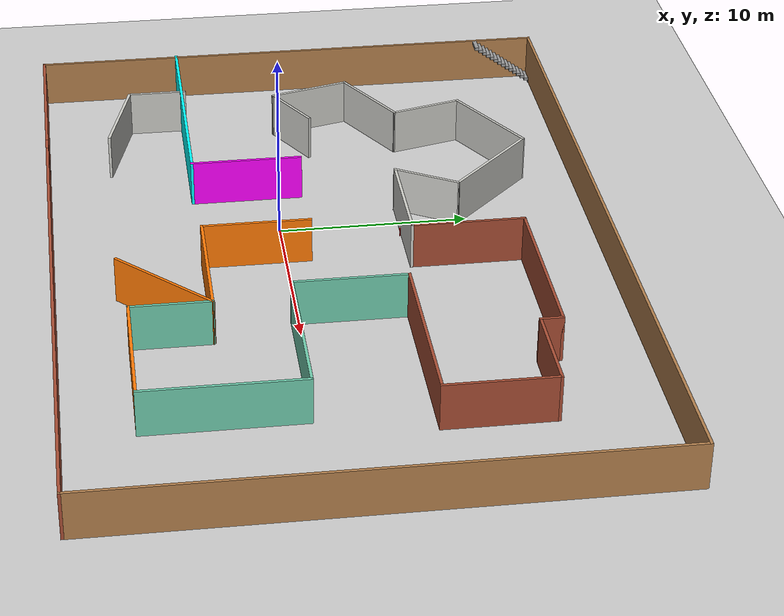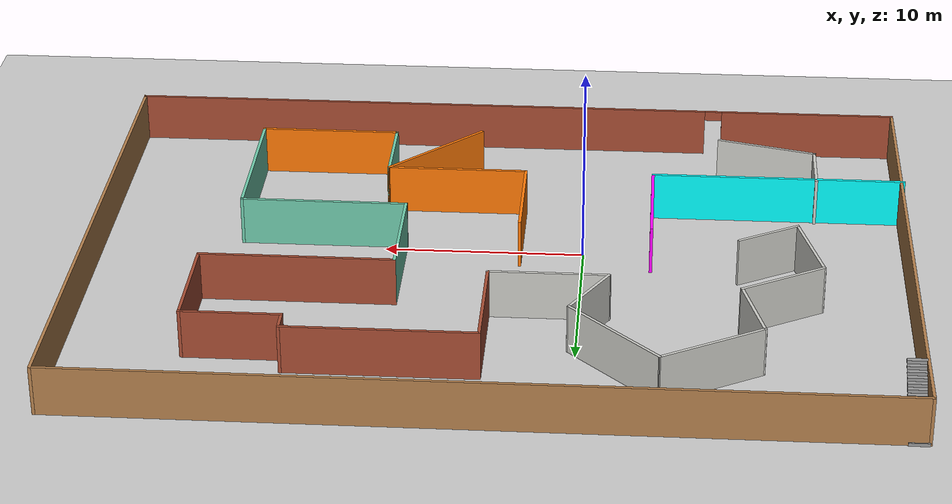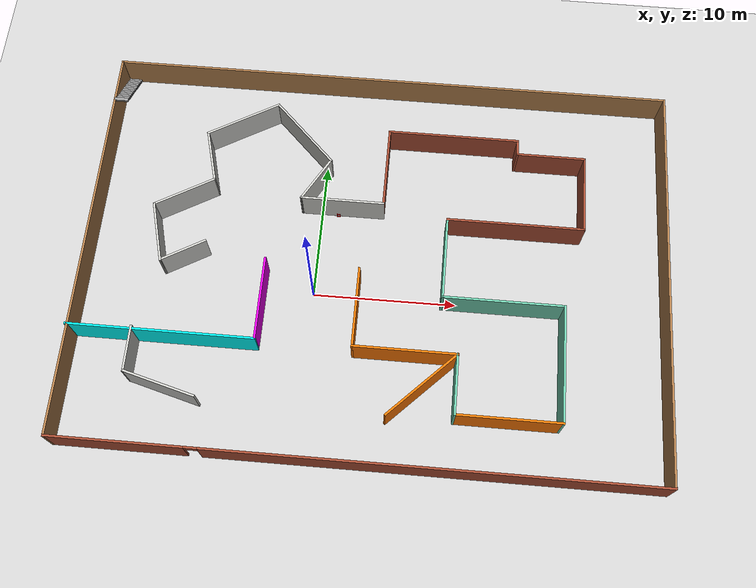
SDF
<sdf version="1.7">
 <world name="default">
  <physics name="1ms" type="ignored">
   <max_step_size>0.001</max_step_size>
   <real_time_factor>1.0</real_time_factor>
  </physics>
  <plugin filename="ignition-gazebo-physics-system" name="ignition::gazebo::systems::Physics"/>
  <plugin filename="ignition-gazebo-user-commands-system" name="ignition::gazebo::systems::UserCommands"/>
  <plugin filename="ignition-gazebo-scene-broadcaster-system" name="ignition::gazebo::systems::SceneBroadcaster"/>
  <plugin filename="ignition-gazebo-contact-system" name="ignition::gazebo::systems::Contact"/>
  <light type="directional" name="sun">
   <pose>0 0 10 0 0 0</pose>
   <diffuse>0.8 0.8 0.8 1</diffuse>
   <specular>0.2 0.2 0.2 1</specular>
   <attenuation>
    <range>1000</range>
    <constant>0.9</constant>
    <linear>0.01</linear>
    <quadratic>0.001</quadratic>
   </attenuation>
   <direction>-0.5 0.1 -0.9</direction>
  </light>
  <model name="ground_plane">
   <static>true</static>
   <link name="link">
    <collision name="collision">
     <geometry><plane><normal>0 0 1</normal><size>100 100</size></plane></geometry>
    </collision>
    <visual name="visual">
     <geometry><plane><normal>0 0 1</normal><size>100 100</size></plane></geometry>
     <material>
      <ambient>0.8 0.8 0.8 1</ambient>
      <diffuse>0.8 0.8 0.8 1</diffuse>
      <specular>0.8 0.8 0.8 1</specular>
     </material>
    </visual>
   </link>
  </model>
  <gravity>0 0 -9.8</gravity>
  <magnetic_field>6e-06 2.3e-05 -4.2e-05</magnetic_field>
  <atmosphere type="adiabatic"/>
  <physics type="ode">
   <max_step_size>0.001</max_step_size>
   <real_time_factor>1</real_time_factor>
   <real_time_update_rate>1000</real_time_update_rate>
  </physics>
  <scene><ambient>0.4 0.4 0.4 1</ambient><background>0.7 0.7 0.7 1</background><shadows>1</shadows></scene>
  <audio><device>default</device></audio>
  <spherical_coordinates>
   <surface_model>EARTH_WGS84</surface_model>
   <latitude_deg>0</latitude_deg>
   <longitude_deg>0</longitude_deg>
   <elevation>0</elevation>
   <heading_deg>0</heading_deg>
  </spherical_coordinates>
  <model name="AMR_navigation_world">
   <link name="Stairs_0">
    <visual name="Stairs_0_Visual_0">
     <pose>-19.7483 14.2861 0.083333 0 -0 0</pose>
     <geometry><box><size>1 0.233333 0.166667</size></box></geometry>
     <material>
      <script><uri>file://media/materials/scripts/gazebo.material</uri><name>Gazebo/Grey</name></script>
      <ambient>1 1 1 1</ambient>
      <shader type="pixel"/>
     </material>
     <meta><layer>0</layer></meta>
    </visual>
    <visual name="Stairs_0_Visual_1">
     <pose>-19.7483 14.0528 0.25 0 -0 0</pose>
     <geometry><box><size>1 0.233333 0.166667</size></box></geometry>
     <material>
      <script><uri>file://media/materials/scripts/gazebo.material</uri><name>Gazebo/Grey</name></script>
      <ambient>1 1 1 1</ambient>
      <shader type="pixel"/>
     </material>
     <meta><layer>0</layer></meta>
    </visual>
    <visual name="Stairs_0_Visual_2">
     <pose>-19.7483 13.8195 0.416667 0 -0 0</pose>
     <geometry><box><size>1 0.233333 0.166667</size></box></geometry>
     <material>
      <script><uri>file://media/materials/scripts/gazebo.material</uri><name>Gazebo/Grey</name></script>
      <ambient>1 1 1 1</ambient>
      <shader type="pixel"/>
     </material>
     <meta><layer>0</layer></meta>
    </visual>
    <visual name="Stairs_0_Visual_3">
     <pose>-19.7483 13.5861 0.583333 0 -0 0</pose>
     <geometry><box><size>1 0.233333 0.166667</size></box></geometry>
     <material>
      <script><uri>file://media/materials/scripts/gazebo.material</uri><name>Gazebo/Grey</name></script>
      <ambient>1 1 1 1</ambient>
      <shader type="pixel"/>
     </material>
     <meta><layer>0</layer></meta>
    </visual>
    <visual name="Stairs_0_Visual_4">
     <pose>-19.7483 13.3528 0.75 0 -0 0</pose>
     <geometry><box><size>1 0.233333 0.166667</size></box></geometry>
     <material>
      <script><uri>file://media/materials/scripts/gazebo.material</uri><name>Gazebo/Grey</name></script>
      <ambient>1 1 1 1</ambient>
      <shader type="pixel"/>
     </material>
     <meta><layer>0</layer></meta>
    </visual>
    <visual name="Stairs_0_Visual_5">
     <pose>-19.7483 13.1195 0.916667 0 -0 0</pose>
     <geometry><box><size>1 0.233333 0.166667</size></box></geometry>
     <material>
      <script><uri>file://media/materials/scripts/gazebo.material</uri><name>Gazebo/Grey</name></script>
      <ambient>1 1 1 1</ambient>
      <shader type="pixel"/>
     </material>
     <meta><layer>0</layer></meta>
    </visual>
    <visual name="Stairs_0_Visual_6">
     <pose>-19.7483 12.8861 1.08333 0 -0 0</pose>
     <geometry><box><size>1 0.233333 0.166667</size></box></geometry>
     <material>
      <script><uri>file://media/materials/scripts/gazebo.material</uri><name>Gazebo/Grey</name></script>
      <ambient>1 1 1 1</ambient>
      <shader type="pixel"/>
     </material>
     <meta><layer>0</layer></meta>
    </visual>
    <visual name="Stairs_0_Visual_7">
     <pose>-19.7483 12.6528 1.25 0 -0 0</pose>
     <geometry><box><size>1 0.233333 0.166667</size></box></geometry>
     <material>
      <script><uri>file://media/materials/scripts/gazebo.material</uri><name>Gazebo/Grey</name></script>
      <ambient>1 1 1 1</ambient>
      <shader type="pixel"/>
     </material>
     <meta><layer>0</layer></meta>
    </visual>
    <visual name="Stairs_0_Visual_8">
     <pose>-19.7483 12.4195 1.41667 0 -0 0</pose>
     <geometry><box><size>1 0.233333 0.166667</size></box></geometry>
     <material>
      <script><uri>file://media/materials/scripts/gazebo.material</uri><name>Gazebo/Grey</name></script>
      <ambient>1 1 1 1</ambient>
      <shader type="pixel"/>
     </material>
     <meta><layer>0</layer></meta>
    </visual>
    <visual name="Stairs_0_Visual_9">
     <pose>-19.7483 12.1861 1.58333 0 -0 0</pose>
     <geometry><box><size>1 0.233333 0.166667</size></box></geometry>
     <material>
      <script><uri>file://media/materials/scripts/gazebo.material</uri><name>Gazebo/Grey</name></script>
      <ambient>1 1 1 1</ambient>
      <shader type="pixel"/>
     </material>
     <meta><layer>0</layer></meta>
    </visual>
    <visual name="Stairs_0_Visual_10">
     <pose>-19.7483 11.9528 1.75 0 -0 0</pose>
     <geometry><box><size>1 0.233333 0.166667</size></box></geometry>
     <material>
      <script><uri>file://media/materials/scripts/gazebo.material</uri><name>Gazebo/Grey</name></script>
      <ambient>1 1 1 1</ambient>
      <shader type="pixel"/>
     </material>
     <meta><layer>0</layer></meta>
    </visual>
    <visual name="Stairs_0_Visual_11">
     <pose>-19.7483 11.7195 1.91667 0 -0 0</pose>
     <geometry><box><size>1 0.233333 0.166667</size></box></geometry>
     <material>
      <script><uri>file://media/materials/scripts/gazebo.material</uri><name>Gazebo/Grey</name></script>
      <ambient>1 1 1 1</ambient>
      <shader type="pixel"/>
     </material>
     <meta><layer>0</layer></meta>
    </visual>
    <visual name="Stairs_0_Visual_12">
     <pose>-19.7483 11.4861 2.08333 0 -0 0</pose>
     <geometry><box><size>1 0.233333 0.166667</size></box></geometry>
     <material>
      <script><uri>file://media/materials/scripts/gazebo.material</uri><name>Gazebo/Grey</name></script>
      <ambient>1 1 1 1</ambient>
      <shader type="pixel"/>
     </material>
     <meta><layer>0</layer></meta>
    </visual>
    <visual name="Stairs_0_Visual_13">
     <pose>-19.7483 11.2528 2.25 0 -0 0</pose>
     <geometry><box><size>1 0.233333 0.166667</size></box></geometry>
     <material>
      <script><uri>file://media/materials/scripts/gazebo.material</uri><name>Gazebo/Grey</name></script>
      <ambient>1 1 1 1</ambient>
      <shader type="pixel"/>
     </material>
     <meta><layer>0</layer></meta>
    </visual>
    <visual name="Stairs_0_Visual_14">
     <pose>-19.7483 11.0195 2.41667 0 -0 0</pose>
     <geometry><box><size>1 0.233333 0.166667</size></box></geometry>
     <material>
      <script><uri>file://media/materials/scripts/gazebo.material</uri><name>Gazebo/Grey</name></script>
      <ambient>1 1 1 1</ambient>
      <shader type="pixel"/>
     </material>
     <meta><layer>0</layer></meta>
    </visual>
    <collision name="Stairs_0_Collision_0">
     <pose>-19.7483 14.2861 0.083333 0 -0 0</pose>
     <geometry><box><size>1 0.233333 0.166667</size></box></geometry>
     <surface>
      <friction>
       <ode><mu>1</mu><mu2>1</mu2><fdir1>0 0 0</fdir1><slip1>0</slip1><slip2>0</slip2></ode>
       <torsional>
        <coefficient>1</coefficient>
        <patch_radius>0</patch_radius>
        <surface_radius>0</surface_radius>
        <use_patch_radius>1</use_patch_radius>
        <ode><slip>0</slip></ode>
       </torsional>
      </friction>
      <bounce><restitution_coefficient>0</restitution_coefficient><threshold>1e+06</threshold></bounce>
      <contact>
       <collide_without_contact>0</collide_without_contact>
       <collide_without_contact_bitmask>1</collide_without_contact_bitmask>
       <collide_bitmask>1</collide_bitmask>
       <ode>
        <soft_cfm>0</soft_cfm>
        <soft_erp>0.2</soft_erp>
        <kp>1e+13</kp>
        <kd>1</kd>
        <max_vel>0.01</max_vel>
        <min_depth>0</min_depth>
       </ode>
       <bullet>
        <split_impulse>1</split_impulse>
        <split_impulse_penetration_threshold>-0.01</split_impulse_penetration_threshold>
        <soft_cfm>0</soft_cfm>
        <soft_erp>0.2</soft_erp>
        <kp>1e+13</kp>
        <kd>1</kd>
       </bullet>
      </contact>
     </surface>
    </collision>
    <collision name="Stairs_0_Collision_1">
     <pose>-19.7483 14.0528 0.25 0 -0 0</pose>
     <geometry><box><size>1 0.233333 0.166667</size></box></geometry>
     <surface>
      <friction>
       <ode><mu>1</mu><mu2>1</mu2><fdir1>0 0 0</fdir1><slip1>0</slip1><slip2>0</slip2></ode>
       <torsional>
        <coefficient>1</coefficient>
        <patch_radius>0</patch_radius>
        <surface_radius>0</surface_radius>
        <use_patch_radius>1</use_patch_radius>
        <ode><slip>0</slip></ode>
       </torsional>
      </friction>
      <bounce><restitution_coefficient>0</restitution_coefficient><threshold>1e+06</threshold></bounce>
      <contact>
       <collide_without_contact>0</collide_without_contact>
       <collide_without_contact_bitmask>1</collide_without_contact_bitmask>
       <collide_bitmask>1</collide_bitmask>
       <ode>
        <soft_cfm>0</soft_cfm>
        <soft_erp>0.2</soft_erp>
        <kp>1e+13</kp>
        <kd>1</kd>
        <max_vel>0.01</max_vel>
        <min_depth>0</min_depth>
       </ode>
       <bullet>
        <split_impulse>1</split_impulse>
        <split_impulse_penetration_threshold>-0.01</split_impulse_penetration_threshold>
        <soft_cfm>0</soft_cfm>
        <soft_erp>0.2</soft_erp>
        <kp>1e+13</kp>
        <kd>1</kd>
       </bullet>
      </contact>
     </surface>
    </collision>
    <collision name="Stairs_0_Collision_2">
     <pose>-19.7483 13.8195 0.416667 0 -0 0</pose>
     <geometry><box><size>1 0.233333 0.166667</size></box></geometry>
     <surface>
      <friction>
       <ode><mu>1</mu><mu2>1</mu2><fdir1>0 0 0</fdir1><slip1>0</slip1><slip2>0</slip2></ode>
       <torsional>
        <coefficient>1</coefficient>
        <patch_radius>0</patch_radius>
        <surface_radius>0</surface_radius>
        <use_patch_radius>1</use_patch_radius>
        <ode><slip>0</slip></ode>
       </torsional>
      </friction>
      <bounce><restitution_coefficient>0</restitution_coefficient><threshold>1e+06</threshold></bounce>
      <contact>
       <collide_without_contact>0</collide_without_contact>
       <collide_without_contact_bitmask>1</collide_without_contact_bitmask>
       <collide_bitmask>1</collide_bitmask>
       <ode>
        <soft_cfm>0</soft_cfm>
        <soft_erp>0.2</soft_erp>
        <kp>1e+13</kp>
        <kd>1</kd>
        <max_vel>0.01</max_vel>
        <min_depth>0</min_depth>
       </ode>
       <bullet>
        <split_impulse>1</split_impulse>
        <split_impulse_penetration_threshold>-0.01</split_impulse_penetration_threshold>
        <soft_cfm>0</soft_cfm>
        <soft_erp>0.2</soft_erp>
        <kp>1e+13</kp>
        <kd>1</kd>
       </bullet>
      </contact>
     </surface>
    </collision>
    <collision name="Stairs_0_Collision_3">
     <pose>-19.7483 13.5861 0.583333 0 -0 0</pose>
     <geometry><box><size>1 0.233333 0.166667</size></box></geometry>
     <surface>
      <friction>
       <ode><mu>1</mu><mu2>1</mu2><fdir1>0 0 0</fdir1><slip1>0</slip1><slip2>0</slip2></ode>
       <torsional>
        <coefficient>1</coefficient>
        <patch_radius>0</patch_radius>
        <surface_radius>0</surface_radius>
        <use_patch_radius>1</use_patch_radius>
        <ode><slip>0</slip></ode>
       </torsional>
      </friction>
      <bounce><restitution_coefficient>0</restitution_coefficient><threshold>1e+06</threshold></bounce>
      <contact>
       <collide_without_contact>0</collide_without_contact>
       <collide_without_contact_bitmask>1</collide_without_contact_bitmask>
       <collide_bitmask>1</collide_bitmask>
       <ode>
        <soft_cfm>0</soft_cfm>
        <soft_erp>0.2</soft_erp>
        <kp>1e+13</kp>
        <kd>1</kd>
        <max_vel>0.01</max_vel>
        <min_depth>0</min_depth>
       </ode>
       <bullet>
        <split_impulse>1</split_impulse>
        <split_impulse_penetration_threshold>-0.01</split_impulse_penetration_threshold>
        <soft_cfm>0</soft_cfm>
        <soft_erp>0.2</soft_erp>
        <kp>1e+13</kp>
        <kd>1</kd>
       </bullet>
      </contact>
     </surface>
    </collision>
    <collision name="Stairs_0_Collision_4">
     <pose>-19.7483 13.3528 0.75 0 -0 0</pose>
     <geometry><box><size>1 0.233333 0.166667</size></box></geometry>
     <surface>
      <friction>
       <ode><mu>1</mu><mu2>1</mu2><fdir1>0 0 0</fdir1><slip1>0</slip1><slip2>0</slip2></ode>
       <torsional>
        <coefficient>1</coefficient>
        <patch_radius>0</patch_radius>
        <surface_radius>0</surface_radius>
        <use_patch_radius>1</use_patch_radius>
        <ode><slip>0</slip></ode>
       </torsional>
      </friction>
      <bounce><restitution_coefficient>0</restitution_coefficient><threshold>1e+06</threshold></bounce>
      <contact>
       <collide_without_contact>0</collide_without_contact>
       <collide_without_contact_bitmask>1</collide_without_contact_bitmask>
       <collide_bitmask>1</collide_bitmask>
       <ode>
        <soft_cfm>0</soft_cfm>
        <soft_erp>0.2</soft_erp>
        <kp>1e+13</kp>
        <kd>1</kd>
        <max_vel>0.01</max_vel>
        <min_depth>0</min_depth>
       </ode>
       <bullet>
        <split_impulse>1</split_impulse>
        <split_impulse_penetration_threshold>-0.01</split_impulse_penetration_threshold>
        <soft_cfm>0</soft_cfm>
        <soft_erp>0.2</soft_erp>
        <kp>1e+13</kp>
        <kd>1</kd>
       </bullet>
      </contact>
     </surface>
    </collision>
    <collision name="Stairs_0_Collision_5">
     <pose>-19.7483 13.1195 0.916667 0 -0 0</pose>
     <geometry><box><size>1 0.233333 0.166667</size></box></geometry>
     <surface>
      <friction>
       <ode><mu>1</mu><mu2>1</mu2><fdir1>0 0 0</fdir1><slip1>0</slip1><slip2>0</slip2></ode>
       <torsional>
        <coefficient>1</coefficient>
        <patch_radius>0</patch_radius>
        <surface_radius>0</surface_radius>
        <use_patch_radius>1</use_patch_radius>
        <ode><slip>0</slip></ode>
       </torsional>
      </friction>
      <bounce><restitution_coefficient>0</restitution_coefficient><threshold>1e+06</threshold></bounce>
      <contact>
       <collide_without_contact>0</collide_without_contact>
       <collide_without_contact_bitmask>1</collide_without_contact_bitmask>
       <collide_bitmask>1</collide_bitmask>
       <ode>
        <soft_cfm>0</soft_cfm>
        <soft_erp>0.2</soft_erp>
        <kp>1e+13</kp>
        <kd>1</kd>
        <max_vel>0.01</max_vel>
        <min_depth>0</min_depth>
       </ode>
       <bullet>
        <split_impulse>1</split_impulse>
        <split_impulse_penetration_threshold>-0.01</split_impulse_penetration_threshold>
        <soft_cfm>0</soft_cfm>
        <soft_erp>0.2</soft_erp>
        <kp>1e+13</kp>
        <kd>1</kd>
       </bullet>
      </contact>
     </surface>
    </collision>
    <collision name="Stairs_0_Collision_6">
     <pose>-19.7483 12.8861 1.08333 0 -0 0</pose>
     <geometry><box><size>1 0.233333 0.166667</size></box></geometry>
     <surface>
      <friction>
       <ode><mu>1</mu><mu2>1</mu2><fdir1>0 0 0</fdir1><slip1>0</slip1><slip2>0</slip2></ode>
       <torsional>
        <coefficient>1</coefficient>
        <patch_radius>0</patch_radius>
        <surface_radius>0</surface_radius>
        <use_patch_radius>1</use_patch_radius>
        <ode><slip>0</slip></ode>
       </torsional>
      </friction>
      <bounce><restitution_coefficient>0</restitution_coefficient><threshold>1e+06</threshold></bounce>
      <contact>
       <collide_without_contact>0</collide_without_contact>
       <collide_without_contact_bitmask>1</collide_without_contact_bitmask>
       <collide_bitmask>1</collide_bitmask>
       <ode>
        <soft_cfm>0</soft_cfm>
        <soft_erp>0.2</soft_erp>
        <kp>1e+13</kp>
        <kd>1</kd>
        <max_vel>0.01</max_vel>
        <min_depth>0</min_depth>
       </ode>
       <bullet>
        <split_impulse>1</split_impulse>
        <split_impulse_penetration_threshold>-0.01</split_impulse_penetration_threshold>
        <soft_cfm>0</soft_cfm>
        <soft_erp>0.2</soft_erp>
        <kp>1e+13</kp>
        <kd>1</kd>
       </bullet>
      </contact>
     </surface>
    </collision>
    <collision name="Stairs_0_Collision_7">
     <pose>-19.7483 12.6528 1.25 0 -0 0</pose>
     <geometry><box><size>1 0.233333 0.166667</size></box></geometry>
     <surface>
      <friction>
       <ode><mu>1</mu><mu2>1</mu2><fdir1>0 0 0</fdir1><slip1>0</slip1><slip2>0</slip2></ode>
       <torsional>
        <coefficient>1</coefficient>
        <patch_radius>0</patch_radius>
        <surface_radius>0</surface_radius>
        <use_patch_radius>1</use_patch_radius>
        <ode><slip>0</slip></ode>
       </torsional>
      </friction>
      <bounce><restitution_coefficient>0</restitution_coefficient><threshold>1e+06</threshold></bounce>
      <contact>
       <collide_without_contact>0</collide_without_contact>
       <collide_without_contact_bitmask>1</collide_without_contact_bitmask>
       <collide_bitmask>1</collide_bitmask>
       <ode>
        <soft_cfm>0</soft_cfm>
        <soft_erp>0.2</soft_erp>
        <kp>1e+13</kp>
        <kd>1</kd>
        <max_vel>0.01</max_vel>
        <min_depth>0</min_depth>
       </ode>
       <bullet>
        <split_impulse>1</split_impulse>
        <split_impulse_penetration_threshold>-0.01</split_impulse_penetration_threshold>
        <soft_cfm>0</soft_cfm>
        <soft_erp>0.2</soft_erp>
        <kp>1e+13</kp>
        <kd>1</kd>
       </bullet>
      </contact>
     </surface>
    </collision>
    <collision name="Stairs_0_Collision_8">
     <pose>-19.7483 12.4195 1.41667 0 -0 0</pose>
     <geometry><box><size>1 0.233333 0.166667</size></box></geometry>
     <surface>
      <friction>
       <ode><mu>1</mu><mu2>1</mu2><fdir1>0 0 0</fdir1><slip1>0</slip1><slip2>0</slip2></ode>
       <torsional>
        <coefficient>1</coefficient>
        <patch_radius>0</patch_radius>
        <surface_radius>0</surface_radius>
        <use_patch_radius>1</use_patch_radius>
        <ode><slip>0</slip></ode>
       </torsional>
      </friction>
      <bounce><restitution_coefficient>0</restitution_coefficient><threshold>1e+06</threshold></bounce>
      <contact>
       <collide_without_contact>0</collide_without_contact>
       <collide_without_contact_bitmask>1</collide_without_contact_bitmask>
       <collide_bitmask>1</collide_bitmask>
       <ode>
        <soft_cfm>0</soft_cfm>
        <soft_erp>0.2</soft_erp>
        <kp>1e+13</kp>
        <kd>1</kd>
        <max_vel>0.01</max_vel>
        <min_depth>0</min_depth>
       </ode>
       <bullet>
        <split_impulse>1</split_impulse>
        <split_impulse_penetration_threshold>-0.01</split_impulse_penetration_threshold>
        <soft_cfm>0</soft_cfm>
        <soft_erp>0.2</soft_erp>
        <kp>1e+13</kp>
        <kd>1</kd>
       </bullet>
      </contact>
     </surface>
    </collision>
    <collision name="Stairs_0_Collision_9">
     <pose>-19.7483 12.1861 1.58333 0 -0 0</pose>
     <geometry><box><size>1 0.233333 0.166667</size></box></geometry>
     <surface>
      <friction>
       <ode><mu>1</mu><mu2>1</mu2><fdir1>0 0 0</fdir1><slip1>0</slip1><slip2>0</slip2></ode>
       <torsional>
        <coefficient>1</coefficient>
        <patch_radius>0</patch_radius>
        <surface_radius>0</surface_radius>
        <use_patch_radius>1</use_patch_radius>
        <ode><slip>0</slip></ode>
       </torsional>
      </friction>
      <bounce><restitution_coefficient>0</restitution_coefficient><threshold>1e+06</threshold></bounce>
      <contact>
       <collide_without_contact>0</collide_without_contact>
       <collide_without_contact_bitmask>1</collide_without_contact_bitmask>
       <collide_bitmask>1</collide_bitmask>
       <ode>
        <soft_cfm>0</soft_cfm>
        <soft_erp>0.2</soft_erp>
        <kp>1e+13</kp>
        <kd>1</kd>
        <max_vel>0.01</max_vel>
        <min_depth>0</min_depth>
       </ode>
       <bullet>
        <split_impulse>1</split_impulse>
        <split_impulse_penetration_threshold>-0.01</split_impulse_penetration_threshold>
        <soft_cfm>0</soft_cfm>
        <soft_erp>0.2</soft_erp>
        <kp>1e+13</kp>
        <kd>1</kd>
       </bullet>
      </contact>
     </surface>
    </collision>
    <collision name="Stairs_0_Collision_10">
     <pose>-19.7483 11.9528 1.75 0 -0 0</pose>
     <geometry><box><size>1 0.233333 0.166667</size></box></geometry>
     <surface>
      <friction>
       <ode><mu>1</mu><mu2>1</mu2><fdir1>0 0 0</fdir1><slip1>0</slip1><slip2>0</slip2></ode>
       <torsional>
        <coefficient>1</coefficient>
        <patch_radius>0</patch_radius>
        <surface_radius>0</surface_radius>
        <use_patch_radius>1</use_patch_radius>
        <ode><slip>0</slip></ode>
       </torsional>
      </friction>
      <bounce><restitution_coefficient>0</restitution_coefficient><threshold>1e+06</threshold></bounce>
      <contact>
       <collide_without_contact>0</collide_without_contact>
       <collide_without_contact_bitmask>1</collide_without_contact_bitmask>
       <collide_bitmask>1</collide_bitmask>
       <ode>
        <soft_cfm>0</soft_cfm>
        <soft_erp>0.2</soft_erp>
        <kp>1e+13</kp>
        <kd>1</kd>
        <max_vel>0.01</max_vel>
        <min_depth>0</min_depth>
       </ode>
       <bullet>
        <split_impulse>1</split_impulse>
        <split_impulse_penetration_threshold>-0.01</split_impulse_penetration_threshold>
        <soft_cfm>0</soft_cfm>
        <soft_erp>0.2</soft_erp>
        <kp>1e+13</kp>
        <kd>1</kd>
       </bullet>
      </contact>
     </surface>
    </collision>
    <collision name="Stairs_0_Collision_11">
     <pose>-19.7483 11.7195 1.91667 0 -0 0</pose>
     <geometry><box><size>1 0.233333 0.166667</size></box></geometry>
     <surface>
      <friction>
       <ode><mu>1</mu><mu2>1</mu2><fdir1>0 0 0</fdir1><slip1>0</slip1><slip2>0</slip2></ode>
       <torsional>
        <coefficient>1</coefficient>
        <patch_radius>0</patch_radius>
        <surface_radius>0</surface_radius>
        <use_patch_radius>1</use_patch_radius>
        <ode><slip>0</slip></ode>
       </torsional>
      </friction>
      <bounce><restitution_coefficient>0</restitution_coefficient><threshold>1e+06</threshold></bounce>
      <contact>
       <collide_without_contact>0</collide_without_contact>
       <collide_without_contact_bitmask>1</collide_without_contact_bitmask>
       <collide_bitmask>1</collide_bitmask>
       <ode>
        <soft_cfm>0</soft_cfm>
        <soft_erp>0.2</soft_erp>
        <kp>1e+13</kp>
        <kd>1</kd>
        <max_vel>0.01</max_vel>
        <min_depth>0</min_depth>
       </ode>
       <bullet>
        <split_impulse>1</split_impulse>
        <split_impulse_penetration_threshold>-0.01</split_impulse_penetration_threshold>
        <soft_cfm>0</soft_cfm>
        <soft_erp>0.2</soft_erp>
        <kp>1e+13</kp>
        <kd>1</kd>
       </bullet>
      </contact>
     </surface>
    </collision>
    <collision name="Stairs_0_Collision_12">
     <pose>-19.7483 11.4861 2.08333 0 -0 0</pose>
     <geometry><box><size>1 0.233333 0.166667</size></box></geometry>
     <surface>
      <friction>
       <ode><mu>1</mu><mu2>1</mu2><fdir1>0 0 0</fdir1><slip1>0</slip1><slip2>0</slip2></ode>
       <torsional>
        <coefficient>1</coefficient>
        <patch_radius>0</patch_radius>
        <surface_radius>0</surface_radius>
        <use_patch_radius>1</use_patch_radius>
        <ode><slip>0</slip></ode>
       </torsional>
      </friction>
      <bounce><restitution_coefficient>0</restitution_coefficient><threshold>1e+06</threshold></bounce>
      <contact>
       <collide_without_contact>0</collide_without_contact>
       <collide_without_contact_bitmask>1</collide_without_contact_bitmask>
       <collide_bitmask>1</collide_bitmask>
       <ode>
        <soft_cfm>0</soft_cfm>
        <soft_erp>0.2</soft_erp>
        <kp>1e+13</kp>
        <kd>1</kd>
        <max_vel>0.01</max_vel>
        <min_depth>0</min_depth>
       </ode>
       <bullet>
        <split_impulse>1</split_impulse>
        <split_impulse_penetration_threshold>-0.01</split_impulse_penetration_threshold>
        <soft_cfm>0</soft_cfm>
        <soft_erp>0.2</soft_erp>
        <kp>1e+13</kp>
        <kd>1</kd>
       </bullet>
      </contact>
     </surface>
    </collision>
    <collision name="Stairs_0_Collision_13">
     <pose>-19.7483 11.2528 2.25 0 -0 0</pose>
     <geometry><box><size>1 0.233333 0.166667</size></box></geometry>
     <surface>
      <friction>
       <ode><mu>1</mu><mu2>1</mu2><fdir1>0 0 0</fdir1><slip1>0</slip1><slip2>0</slip2></ode>
       <torsional>
        <coefficient>1</coefficient>
        <patch_radius>0</patch_radius>
        <surface_radius>0</surface_radius>
        <use_patch_radius>1</use_patch_radius>
        <ode><slip>0</slip></ode>
       </torsional>
      </friction>
      <bounce><restitution_coefficient>0</restitution_coefficient><threshold>1e+06</threshold></bounce>
      <contact>
       <collide_without_contact>0</collide_without_contact>
       <collide_without_contact_bitmask>1</collide_without_contact_bitmask>
       <collide_bitmask>1</collide_bitmask>
       <ode>
        <soft_cfm>0</soft_cfm>
        <soft_erp>0.2</soft_erp>
        <kp>1e+13</kp>
        <kd>1</kd>
        <max_vel>0.01</max_vel>
        <min_depth>0</min_depth>
       </ode>
       <bullet>
        <split_impulse>1</split_impulse>
        <split_impulse_penetration_threshold>-0.01</split_impulse_penetration_threshold>
        <soft_cfm>0</soft_cfm>
        <soft_erp>0.2</soft_erp>
        <kp>1e+13</kp>
        <kd>1</kd>
       </bullet>
      </contact>
     </surface>
    </collision>
    <collision name="Stairs_0_Collision_14">
     <pose>-19.7483 11.0195 2.41667 0 -0 0</pose>
     <geometry><box><size>1 0.233333 0.166667</size></box></geometry>
     <surface>
      <friction>
       <ode><mu>1</mu><mu2>1</mu2><fdir1>0 0 0</fdir1><slip1>0</slip1><slip2>0</slip2></ode>
       <torsional>
        <coefficient>1</coefficient>
        <patch_radius>0</patch_radius>
        <surface_radius>0</surface_radius>
        <use_patch_radius>1</use_patch_radius>
        <ode><slip>0</slip></ode>
       </torsional>
      </friction>
      <bounce><restitution_coefficient>0</restitution_coefficient><threshold>1e+06</threshold></bounce>
      <contact>
       <collide_without_contact>0</collide_without_contact>
       <collide_without_contact_bitmask>1</collide_without_contact_bitmask>
       <collide_bitmask>1</collide_bitmask>
       <ode>
        <soft_cfm>0</soft_cfm>
        <soft_erp>0.2</soft_erp>
        <kp>1e+13</kp>
        <kd>1</kd>
        <max_vel>0.01</max_vel>
        <min_depth>0</min_depth>
       </ode>
       <bullet>
        <split_impulse>1</split_impulse>
        <split_impulse_penetration_threshold>-0.01</split_impulse_penetration_threshold>
        <soft_cfm>0</soft_cfm>
        <soft_erp>0.2</soft_erp>
        <kp>1e+13</kp>
        <kd>1</kd>
       </bullet>
      </contact>
     </surface>
    </collision>
   </link>
   <link name="Wall_11">
    <pose>-20.2378 -0.027791 0 0 -0 1.5708</pose>
    <visual name="Wall_11_Visual">
     <pose>0 0 1.25 0 -0 0</pose>
     <geometry><box><size>28.75 0.15 2.5</size></box></geometry>
     <material>
      <script><uri>file://media/materials/scripts/gazebo.material</uri><name>Gazebo/Wood</name></script>
      <ambient>1 0 0 1</ambient>
      <shader type="pixel"/>
     </material>
     <meta><layer>0</layer></meta>
    </visual>
    <collision name="Wall_11_Collision">
     <pose>0 0 1.25 0 -0 0</pose>
     <geometry><box><size>28.75 0.15 2.5</size></box></geometry>
     <surface>
      <friction>
       <ode><mu>1</mu><mu2>1</mu2><fdir1>0 0 0</fdir1><slip1>0</slip1><slip2>0</slip2></ode>
       <torsional>
        <coefficient>1</coefficient>
        <patch_radius>0</patch_radius>
        <surface_radius>0</surface_radius>
        <use_patch_radius>1</use_patch_radius>
        <ode><slip>0</slip></ode>
       </torsional>
      </friction>
      <bounce><restitution_coefficient>0</restitution_coefficient><threshold>1e+06</threshold></bounce>
      <contact>
       <collide_without_contact>0</collide_without_contact>
       <collide_without_contact_bitmask>1</collide_without_contact_bitmask>
       <collide_bitmask>1</collide_bitmask>
       <ode>
        <soft_cfm>0</soft_cfm>
        <soft_erp>0.2</soft_erp>
        <kp>1e+13</kp>
        <kd>1</kd>
        <max_vel>0.01</max_vel>
        <min_depth>0</min_depth>
       </ode>
       <bullet>
        <split_impulse>1</split_impulse>
        <split_impulse_penetration_threshold>-0.01</split_impulse_penetration_threshold>
        <soft_cfm>0</soft_cfm>
        <soft_erp>0.2</soft_erp>
        <kp>1e+13</kp>
        <kd>1</kd>
       </bullet>
      </contact>
     </surface>
    </collision>
   </link>
   <link name="Wall_12">
    <pose>0.062232 14.2722 0 0 -0 0</pose>
    <visual name="Wall_12_Visual">
     <pose>0 0 1.25 0 -0 0</pose>
     <geometry><box><size>40.75 0.15 2.5</size></box></geometry>
     <material>
      <script><uri>file://media/materials/scripts/gazebo.material</uri><name>Gazebo/Wood</name></script>
      <ambient>0 1 0 1</ambient>
      <shader type="pixel"/>
     </material>
     <meta><layer>0</layer></meta>
    </visual>
    <collision name="Wall_12_Collision">
     <pose>0 0 1.25 0 -0 0</pose>
     <geometry><box><size>40.75 0.15 2.5</size></box></geometry>
     <surface>
      <friction>
       <ode><mu>1</mu><mu2>1</mu2><fdir1>0 0 0</fdir1><slip1>0</slip1><slip2>0</slip2></ode>
       <torsional>
        <coefficient>1</coefficient>
        <patch_radius>0</patch_radius>
        <surface_radius>0</surface_radius>
        <use_patch_radius>1</use_patch_radius>
        <ode><slip>0</slip></ode>
       </torsional>
      </friction>
      <bounce><restitution_coefficient>0</restitution_coefficient><threshold>1e+06</threshold></bounce>
      <contact>
       <collide_without_contact>0</collide_without_contact>
       <collide_without_contact_bitmask>1</collide_without_contact_bitmask>
       <collide_bitmask>1</collide_bitmask>
       <ode>
        <soft_cfm>0</soft_cfm>
        <soft_erp>0.2</soft_erp>
        <kp>1e+13</kp>
        <kd>1</kd>
        <max_vel>0.01</max_vel>
        <min_depth>0</min_depth>
       </ode>
       <bullet>
        <split_impulse>1</split_impulse>
        <split_impulse_penetration_threshold>-0.01</split_impulse_penetration_threshold>
        <soft_cfm>0</soft_cfm>
        <soft_erp>0.2</soft_erp>
        <kp>1e+13</kp>
        <kd>1</kd>
       </bullet>
      </contact>
     </surface>
    </collision>
   </link>
   <link name="Wall_13">
    <pose>20.3622 -0.027791 0 0 0 -1.5708</pose>
    <visual name="Wall_13_Visual">
     <pose>0 0 1.25 0 -0 0</pose>
     <geometry><box><size>28.75 0.15 2.5</size></box></geometry>
     <material>
      <script><uri>file://media/materials/scripts/gazebo.material</uri><name>Gazebo/Wood</name></script>
      <ambient>0 0 1 1</ambient>
      <shader type="pixel"/>
     </material>
     <meta><layer>0</layer></meta>
    </visual>
    <collision name="Wall_13_Collision">
     <pose>0 0 1.25 0 -0 0</pose>
     <geometry><box><size>28.75 0.15 2.5</size></box></geometry>
     <surface>
      <friction>
       <ode><mu>1</mu><mu2>1</mu2><fdir1>0 0 0</fdir1><slip1>0</slip1><slip2>0</slip2></ode>
       <torsional>
        <coefficient>1</coefficient>
        <patch_radius>0</patch_radius>
        <surface_radius>0</surface_radius>
        <use_patch_radius>1</use_patch_radius>
        <ode><slip>0</slip></ode>
       </torsional>
      </friction>
      <bounce><restitution_coefficient>0</restitution_coefficient><threshold>1e+06</threshold></bounce>
      <contact>
       <collide_without_contact>0</collide_without_contact>
       <collide_without_contact_bitmask>1</collide_without_contact_bitmask>
       <collide_bitmask>1</collide_bitmask>
       <ode>
        <soft_cfm>0</soft_cfm>
        <soft_erp>0.2</soft_erp>
        <kp>1e+13</kp>
        <kd>1</kd>
        <max_vel>0.01</max_vel>
        <min_depth>0</min_depth>
       </ode>
       <bullet>
        <split_impulse>1</split_impulse>
        <split_impulse_penetration_threshold>-0.01</split_impulse_penetration_threshold>
        <soft_cfm>0</soft_cfm>
        <soft_erp>0.2</soft_erp>
        <kp>1e+13</kp>
        <kd>1</kd>
       </bullet>
      </contact>
     </surface>
    </collision>
   </link>
   <link name="Wall_14">
    <pose>0.062232 -14.3278 0 0 -0 3.14159</pose>
    <visual name="Wall_14_Visual_0">
     <pose>-5.04987 0 1.25 0 -0 0</pose>
     <geometry><box><size>30.6503 0.15 2.5</size></box></geometry>
     <material>
      <script><uri>file://media/materials/scripts/gazebo.material</uri><name>Gazebo/Bricks</name></script>
      <ambient>1 1 0 1</ambient>
      <shader type="pixel"/>
     </material>
     <meta><layer>0</layer></meta>
    </visual>
    <visual name="Wall_14_Visual_1">
     <pose>15.7751 0 1.25 0 -0 0</pose>
     <geometry><box><size>9.19974 0.15 2.5</size></box></geometry>
     <material>
      <script><uri>file://media/materials/scripts/gazebo.material</uri><name>Gazebo/Bricks</name></script>
      <ambient>1 1 1 1</ambient>
      <shader type="pixel"/>
     </material>
     <meta><layer>0</layer></meta>
    </visual>
    <visual name="Wall_14_Visual_2">
     <pose>10.7253 0 2.25 0 -0 0</pose>
     <geometry><box><size>0.9 0.15 0.5</size></box></geometry>
     <material>
      <script><uri>file://media/materials/scripts/gazebo.material</uri><name>Gazebo/Bricks</name></script>
      <ambient>1 1 1 1</ambient>
      <shader type="pixel"/>
     </material>
     <meta><layer>0</layer></meta>
    </visual>
    <collision name="Wall_14_Collision_0">
     <pose>-5.04987 0 1.25 0 -0 0</pose>
     <geometry><box><size>30.6503 0.15 2.5</size></box></geometry>
     <surface>
      <friction>
       <ode><mu>1</mu><mu2>1</mu2><fdir1>0 0 0</fdir1><slip1>0</slip1><slip2>0</slip2></ode>
       <torsional>
        <coefficient>1</coefficient>
        <patch_radius>0</patch_radius>
        <surface_radius>0</surface_radius>
        <use_patch_radius>1</use_patch_radius>
        <ode><slip>0</slip></ode>
       </torsional>
      </friction>
      <bounce><restitution_coefficient>0</restitution_coefficient><threshold>1e+06</threshold></bounce>
      <contact>
       <collide_without_contact>0</collide_without_contact>
       <collide_without_contact_bitmask>1</collide_without_contact_bitmask>
       <collide_bitmask>1</collide_bitmask>
       <ode>
        <soft_cfm>0</soft_cfm>
        <soft_erp>0.2</soft_erp>
        <kp>1e+13</kp>
        <kd>1</kd>
        <max_vel>0.01</max_vel>
        <min_depth>0</min_depth>
       </ode>
       <bullet>
        <split_impulse>1</split_impulse>
        <split_impulse_penetration_threshold>-0.01</split_impulse_penetration_threshold>
        <soft_cfm>0</soft_cfm>
        <soft_erp>0.2</soft_erp>
        <kp>1e+13</kp>
        <kd>1</kd>
       </bullet>
      </contact>
     </surface>
    </collision>
    <collision name="Wall_14_Collision_1">
     <pose>15.7751 0 1.25 0 -0 0</pose>
     <geometry><box><size>9.19974 0.15 2.5</size></box></geometry>
     <surface>
      <friction>
       <ode><mu>1</mu><mu2>1</mu2><fdir1>0 0 0</fdir1><slip1>0</slip1><slip2>0</slip2></ode>
       <torsional>
        <coefficient>1</coefficient>
        <patch_radius>0</patch_radius>
        <surface_radius>0</surface_radius>
        <use_patch_radius>1</use_patch_radius>
        <ode><slip>0</slip></ode>
       </torsional>
      </friction>
      <bounce><restitution_coefficient>0</restitution_coefficient><threshold>1e+06</threshold></bounce>
      <contact>
       <collide_without_contact>0</collide_without_contact>
       <collide_without_contact_bitmask>1</collide_without_contact_bitmask>
       <collide_bitmask>1</collide_bitmask>
       <ode>
        <soft_cfm>0</soft_cfm>
        <soft_erp>0.2</soft_erp>
        <kp>1e+13</kp>
        <kd>1</kd>
        <max_vel>0.01</max_vel>
        <min_depth>0</min_depth>
       </ode>
       <bullet>
        <split_impulse>1</split_impulse>
        <split_impulse_penetration_threshold>-0.01</split_impulse_penetration_threshold>
        <soft_cfm>0</soft_cfm>
        <soft_erp>0.2</soft_erp>
        <kp>1e+13</kp>
        <kd>1</kd>
       </bullet>
      </contact>
     </surface>
    </collision>
    <collision name="Wall_14_Collision_2">
     <pose>10.7253 0 2.25 0 -0 0</pose>
     <geometry><box><size>0.9 0.15 0.5</size></box></geometry>
     <surface>
      <friction>
       <ode><mu>1</mu><mu2>1</mu2><fdir1>0 0 0</fdir1><slip1>0</slip1><slip2>0</slip2></ode>
       <torsional>
        <coefficient>1</coefficient>
        <patch_radius>0</patch_radius>
        <surface_radius>0</surface_radius>
        <use_patch_radius>1</use_patch_radius>
        <ode><slip>0</slip></ode>
       </torsional>
      </friction>
      <bounce><restitution_coefficient>0</restitution_coefficient><threshold>1e+06</threshold></bounce>
      <contact>
       <collide_without_contact>0</collide_without_contact>
       <collide_without_contact_bitmask>1</collide_without_contact_bitmask>
       <collide_bitmask>1</collide_bitmask>
       <ode>
        <soft_cfm>0</soft_cfm>
        <soft_erp>0.2</soft_erp>
        <kp>1e+13</kp>
        <kd>1</kd>
        <max_vel>0.01</max_vel>
        <min_depth>0</min_depth>
       </ode>
       <bullet>
        <split_impulse>1</split_impulse>
        <split_impulse_penetration_threshold>-0.01</split_impulse_penetration_threshold>
        <soft_cfm>0</soft_cfm>
        <soft_erp>0.2</soft_erp>
        <kp>1e+13</kp>
        <kd>1</kd>
       </bullet>
      </contact>
     </surface>
    </collision>
   </link>
   <link name="Wall_16">
    <pose>-7.51223 -3.73191 0 0 0 -1.5708</pose>
    <visual name="Wall_16_Visual">
     <pose>0 0 1.25 0 -0 0</pose>
     <geometry><box><size>6 0.15 2.5</size></box></geometry>
     <material>
      <script><uri>file://media/materials/scripts/gazebo.material</uri><name>Gazebo/Grey</name></script>
      <ambient>1 0 1 1</ambient>
      <shader type="pixel"/>
     </material>
     <meta><layer>0</layer></meta>
    </visual>
    <collision name="Wall_16_Collision">
     <pose>0 0 1.25 0 -0 0</pose>
     <geometry><box><size>6 0.15 2.5</size></box></geometry>
     <surface>
      <friction>
       <ode><mu>1</mu><mu2>1</mu2><fdir1>0 0 0</fdir1><slip1>0</slip1><slip2>0</slip2></ode>
       <torsional>
        <coefficient>1</coefficient>
        <patch_radius>0</patch_radius>
        <surface_radius>0</surface_radius>
        <use_patch_radius>1</use_patch_radius>
        <ode><slip>0</slip></ode>
       </torsional>
      </friction>
      <bounce><restitution_coefficient>0</restitution_coefficient><threshold>1e+06</threshold></bounce>
      <contact>
       <collide_without_contact>0</collide_without_contact>
       <collide_without_contact_bitmask>1</collide_without_contact_bitmask>
       <collide_bitmask>1</collide_bitmask>
       <ode>
        <soft_cfm>0</soft_cfm>
        <soft_erp>0.2</soft_erp>
        <kp>1e+13</kp>
        <kd>1</kd>
        <max_vel>0.01</max_vel>
        <min_depth>0</min_depth>
       </ode>
       <bullet>
        <split_impulse>1</split_impulse>
        <split_impulse_penetration_threshold>-0.01</split_impulse_penetration_threshold>
        <soft_cfm>0</soft_cfm>
        <soft_erp>0.2</soft_erp>
        <kp>1e+13</kp>
        <kd>1</kd>
       </bullet>
      </contact>
     </surface>
    </collision>
   </link>
   <link name="Wall_17">
    <pose>-13.9372 -6.65691 0 0 -0 3.14159</pose>
    <visual name="Wall_17_Visual">
     <pose>0 0 1.25 0 -0 0</pose>
     <geometry><box><size>13 0.15 2.5</size></box></geometry>
     <material>
      <script><uri>file://media/materials/scripts/gazebo.material</uri><name>Gazebo/Grey</name></script>
      <ambient>0 1 1 1</ambient>
      <shader type="pixel"/>
     </material>
     <meta><layer>0</layer></meta>
    </visual>
    <collision name="Wall_17_Collision">
     <pose>0 0 1.25 0 -0 0</pose>
     <geometry><box><size>13 0.15 2.5</size></box></geometry>
     <surface>
      <friction>
       <ode><mu>1</mu><mu2>1</mu2><fdir1>0 0 0</fdir1><slip1>0</slip1><slip2>0</slip2></ode>
       <torsional>
        <coefficient>1</coefficient>
        <patch_radius>0</patch_radius>
        <surface_radius>0</surface_radius>
        <use_patch_radius>1</use_patch_radius>
        <ode><slip>0</slip></ode>
       </torsional>
      </friction>
      <bounce><restitution_coefficient>0</restitution_coefficient><threshold>1e+06</threshold></bounce>
      <contact>
       <collide_without_contact>0</collide_without_contact>
       <collide_without_contact_bitmask>1</collide_without_contact_bitmask>
       <collide_bitmask>1</collide_bitmask>
       <ode>
        <soft_cfm>0</soft_cfm>
        <soft_erp>0.2</soft_erp>
        <kp>1e+13</kp>
        <kd>1</kd>
        <max_vel>0.01</max_vel>
        <min_depth>0</min_depth>
       </ode>
       <bullet>
        <split_impulse>1</split_impulse>
        <split_impulse_penetration_threshold>-0.01</split_impulse_penetration_threshold>
        <soft_cfm>0</soft_cfm>
        <soft_erp>0.2</soft_erp>
        <kp>1e+13</kp>
        <kd>1</kd>
       </bullet>
      </contact>
     </surface>
    </collision>
   </link>
   <link name="Wall_19">
    <pose>-0.935334 -3.82104 0 0 0 -1.5708</pose>
    <visual name="Wall_19_Visual">
     <pose>0 0 1.25 0 -0 0</pose>
     <geometry><box><size>5.75 0.15 2.5</size></box></geometry>
     <material>
      <script><uri>file://media/materials/scripts/gazebo.material</uri><name>Gazebo/Grey</name></script>
      <ambient>0.996078 0.47451 0.0196078 1</ambient>
      <shader type="pixel"/>
     </material>
     <meta><layer>0</layer></meta>
    </visual>
    <collision name="Wall_19_Collision">
     <pose>0 0 1.25 0 -0 0</pose>
     <geometry><box><size>5.75 0.15 2.5</size></box></geometry>
     <surface>
      <friction>
       <ode><mu>1</mu><mu2>1</mu2><fdir1>0 0 0</fdir1><slip1>0</slip1><slip2>0</slip2></ode>
       <torsional>
        <coefficient>1</coefficient>
        <patch_radius>0</patch_radius>
        <surface_radius>0</surface_radius>
        <use_patch_radius>1</use_patch_radius>
        <ode><slip>0</slip></ode>
       </torsional>
      </friction>
      <bounce><restitution_coefficient>0</restitution_coefficient><threshold>1e+06</threshold></bounce>
      <contact>
       <collide_without_contact>0</collide_without_contact>
       <collide_without_contact_bitmask>1</collide_without_contact_bitmask>
       <collide_bitmask>1</collide_bitmask>
       <ode>
        <soft_cfm>0</soft_cfm>
        <soft_erp>0.2</soft_erp>
        <kp>1e+13</kp>
        <kd>1</kd>
        <max_vel>0.01</max_vel>
        <min_depth>0</min_depth>
       </ode>
       <bullet>
        <split_impulse>1</split_impulse>
        <split_impulse_penetration_threshold>-0.01</split_impulse_penetration_threshold>
        <soft_cfm>0</soft_cfm>
        <soft_erp>0.2</soft_erp>
        <kp>1e+13</kp>
        <kd>1</kd>
       </bullet>
      </contact>
     </surface>
    </collision>
   </link>
   <link name="Wall_20">
    <pose>2.61467 -6.62104 0 0 -0 0</pose>
    <visual name="Wall_20_Visual">
     <pose>0 0 1.25 0 -0 0</pose>
     <geometry><box><size>7.25 0.15 2.5</size></box></geometry>
     <material>
      <script><uri>file://media/materials/scripts/gazebo.material</uri><name>Gazebo/Grey</name></script>
      <ambient>0.996078 0.47451 0.0196078 1</ambient>
      <shader type="pixel"/>
     </material>
     <meta><layer>0</layer></meta>
    </visual>
    <collision name="Wall_20_Collision">
     <pose>0 0 1.25 0 -0 0</pose>
     <geometry><box><size>7.25 0.15 2.5</size></box></geometry>
     <surface>
      <friction>
       <ode><mu>1</mu><mu2>1</mu2><fdir1>0 0 0</fdir1><slip1>0</slip1><slip2>0</slip2></ode>
       <torsional>
        <coefficient>1</coefficient>
        <patch_radius>0</patch_radius>
        <surface_radius>0</surface_radius>
        <use_patch_radius>1</use_patch_radius>
        <ode><slip>0</slip></ode>
       </torsional>
      </friction>
      <bounce><restitution_coefficient>0</restitution_coefficient><threshold>1e+06</threshold></bounce>
      <contact>
       <collide_without_contact>0</collide_without_contact>
       <collide_without_contact_bitmask>1</collide_without_contact_bitmask>
       <collide_bitmask>1</collide_bitmask>
       <ode>
        <soft_cfm>0</soft_cfm>
        <soft_erp>0.2</soft_erp>
        <kp>1e+13</kp>
        <kd>1</kd>
        <max_vel>0.01</max_vel>
        <min_depth>0</min_depth>
       </ode>
       <bullet>
        <split_impulse>1</split_impulse>
        <split_impulse_penetration_threshold>-0.01</split_impulse_penetration_threshold>
        <soft_cfm>0</soft_cfm>
        <soft_erp>0.2</soft_erp>
        <kp>1e+13</kp>
        <kd>1</kd>
       </bullet>
      </contact>
     </surface>
    </collision>
   </link>
   <link name="Wall_21">
    <pose>6.16467 -8.67104 0 0 0 -1.5708</pose>
    <visual name="Wall_21_Visual">
     <pose>0 0 1.25 0 -0 0</pose>
     <geometry><box><size>4.25 0.15 2.5</size></box></geometry>
     <material>
      <script><uri>file://media/materials/scripts/gazebo.material</uri><name>Gazebo/Grey</name></script>
      <ambient>0.435294 0.796078 0.67451 1</ambient>
      <shader type="pixel"/>
     </material>
     <meta><layer>0</layer></meta>
    </visual>
    <collision name="Wall_21_Collision">
     <pose>0 0 1.25 0 -0 0</pose>
     <geometry><box><size>4.25 0.15 2.5</size></box></geometry>
     <surface>
      <friction>
       <ode><mu>1</mu><mu2>1</mu2><fdir1>0 0 0</fdir1><slip1>0</slip1><slip2>0</slip2></ode>
       <torsional>
        <coefficient>1</coefficient>
        <patch_radius>0</patch_radius>
        <surface_radius>0</surface_radius>
        <use_patch_radius>1</use_patch_radius>
        <ode><slip>0</slip></ode>
       </torsional>
      </friction>
      <bounce><restitution_coefficient>0</restitution_coefficient><threshold>1e+06</threshold></bounce>
      <contact>
       <collide_without_contact>0</collide_without_contact>
       <collide_without_contact_bitmask>1</collide_without_contact_bitmask>
       <collide_bitmask>1</collide_bitmask>
       <ode>
        <soft_cfm>0</soft_cfm>
        <soft_erp>0.2</soft_erp>
        <kp>1e+13</kp>
        <kd>1</kd>
        <max_vel>0.01</max_vel>
        <min_depth>0</min_depth>
       </ode>
       <bullet>
        <split_impulse>1</split_impulse>
        <split_impulse_penetration_threshold>-0.01</split_impulse_penetration_threshold>
        <soft_cfm>0</soft_cfm>
        <soft_erp>0.2</soft_erp>
        <kp>1e+13</kp>
        <kd>1</kd>
       </bullet>
      </contact>
     </surface>
    </collision>
   </link>
   <link name="Wall_22">
    <pose>9.71467 -10.721 0 0 -0 0</pose>
    <visual name="Wall_22_Visual">
     <pose>0 0 1.25 0 -0 0</pose>
     <geometry><box><size>7.25 0.15 2.5</size></box></geometry>
     <material>
      <script><uri>file://media/materials/scripts/gazebo.material</uri><name>Gazebo/Grey</name></script>
      <ambient>0.996078 0.47451 0.0196078 1</ambient>
      <shader type="pixel"/>
     </material>
     <meta><layer>0</layer></meta>
    </visual>
    <collision name="Wall_22_Collision">
     <pose>0 0 1.25 0 -0 0</pose>
     <geometry><box><size>7.25 0.15 2.5</size></box></geometry>
     <surface>
      <friction>
       <ode><mu>1</mu><mu2>1</mu2><fdir1>0 0 0</fdir1><slip1>0</slip1><slip2>0</slip2></ode>
       <torsional>
        <coefficient>1</coefficient>
        <patch_radius>0</patch_radius>
        <surface_radius>0</surface_radius>
        <use_patch_radius>1</use_patch_radius>
        <ode><slip>0</slip></ode>
       </torsional>
      </friction>
      <bounce><restitution_coefficient>0</restitution_coefficient><threshold>1e+06</threshold></bounce>
      <contact>
       <collide_without_contact>0</collide_without_contact>
       <collide_without_contact_bitmask>1</collide_without_contact_bitmask>
       <collide_bitmask>1</collide_bitmask>
       <ode>
        <soft_cfm>0</soft_cfm>
        <soft_erp>0.2</soft_erp>
        <kp>1e+13</kp>
        <kd>1</kd>
        <max_vel>0.01</max_vel>
        <min_depth>0</min_depth>
       </ode>
       <bullet>
        <split_impulse>1</split_impulse>
        <split_impulse_penetration_threshold>-0.01</split_impulse_penetration_threshold>
        <soft_cfm>0</soft_cfm>
        <soft_erp>0.2</soft_erp>
        <kp>1e+13</kp>
        <kd>1</kd>
       </bullet>
      </contact>
     </surface>
    </collision>
   </link>
   <link name="Wall_23">
    <pose>13.2647 -6.67104 0 0 -0 1.5708</pose>
    <visual name="Wall_23_Visual">
     <pose>0 0 1.25 0 -0 0</pose>
     <geometry><box><size>8.25 0.15 2.5</size></box></geometry>
     <material>
      <script><uri>file://media/materials/scripts/gazebo.material</uri><name>Gazebo/Grey</name></script>
      <ambient>0.435294 0.796078 0.67451 1</ambient>
      <shader type="pixel"/>
     </material>
     <meta><layer>0</layer></meta>
    </visual>
    <collision name="Wall_23_Collision">
     <pose>0 0 1.25 0 -0 0</pose>
     <geometry><box><size>8.25 0.15 2.5</size></box></geometry>
     <surface>
      <friction>
       <ode><mu>1</mu><mu2>1</mu2><fdir1>0 0 0</fdir1><slip1>0</slip1><slip2>0</slip2></ode>
       <torsional>
        <coefficient>1</coefficient>
        <patch_radius>0</patch_radius>
        <surface_radius>0</surface_radius>
        <use_patch_radius>1</use_patch_radius>
        <ode><slip>0</slip></ode>
       </torsional>
      </friction>
      <bounce><restitution_coefficient>0</restitution_coefficient><threshold>1e+06</threshold></bounce>
      <contact>
       <collide_without_contact>0</collide_without_contact>
       <collide_without_contact_bitmask>1</collide_without_contact_bitmask>
       <collide_bitmask>1</collide_bitmask>
       <ode>
        <soft_cfm>0</soft_cfm>
        <soft_erp>0.2</soft_erp>
        <kp>1e+13</kp>
        <kd>1</kd>
        <max_vel>0.01</max_vel>
        <min_depth>0</min_depth>
       </ode>
       <bullet>
        <split_impulse>1</split_impulse>
        <split_impulse_penetration_threshold>-0.01</split_impulse_penetration_threshold>
        <soft_cfm>0</soft_cfm>
        <soft_erp>0.2</soft_erp>
        <kp>1e+13</kp>
        <kd>1</kd>
       </bullet>
      </contact>
     </surface>
    </collision>
   </link>
   <link name="Wall_24">
    <pose>9.08967 -2.62104 0 0 -0 3.14159</pose>
    <visual name="Wall_24_Visual">
     <pose>0 0 1.25 0 -0 0</pose>
     <geometry><box><size>8.5 0.15 2.5</size></box></geometry>
     <material>
      <script><uri>file://media/materials/scripts/gazebo.material</uri><name>Gazebo/Grey</name></script>
      <ambient>0.435294 0.796078 0.67451 1</ambient>
      <shader type="pixel"/>
     </material>
     <meta><layer>0</layer></meta>
    </visual>
    <collision name="Wall_24_Collision">
     <pose>0 0 1.25 0 -0 0</pose>
     <geometry><box><size>8.5 0.15 2.5</size></box></geometry>
     <surface>
      <friction>
       <ode><mu>1</mu><mu2>1</mu2><fdir1>0 0 0</fdir1><slip1>0</slip1><slip2>0</slip2></ode>
       <torsional>
        <coefficient>1</coefficient>
        <patch_radius>0</patch_radius>
        <surface_radius>0</surface_radius>
        <use_patch_radius>1</use_patch_radius>
        <ode><slip>0</slip></ode>
       </torsional>
      </friction>
      <bounce><restitution_coefficient>0</restitution_coefficient><threshold>1e+06</threshold></bounce>
      <contact>
       <collide_without_contact>0</collide_without_contact>
       <collide_without_contact_bitmask>1</collide_without_contact_bitmask>
       <collide_bitmask>1</collide_bitmask>
       <ode>
        <soft_cfm>0</soft_cfm>
        <soft_erp>0.2</soft_erp>
        <kp>1e+13</kp>
        <kd>1</kd>
        <max_vel>0.01</max_vel>
        <min_depth>0</min_depth>
       </ode>
       <bullet>
        <split_impulse>1</split_impulse>
        <split_impulse_penetration_threshold>-0.01</split_impulse_penetration_threshold>
        <soft_cfm>0</soft_cfm>
        <soft_erp>0.2</soft_erp>
        <kp>1e+13</kp>
        <kd>1</kd>
       </bullet>
      </contact>
     </surface>
    </collision>
   </link>
   <link name="Wall_25">
    <pose>4.91467 0.303959 0 0 -0 1.5708</pose>
    <visual name="Wall_25_Visual">
     <pose>0 0 1.25 0 -0 0</pose>
     <geometry><box><size>6 0.15 2.5</size></box></geometry>
     <material>
      <script><uri>file://media/materials/scripts/gazebo.material</uri><name>Gazebo/Grey</name></script>
      <ambient>0.435294 0.796078 0.67451 1</ambient>
      <shader type="pixel"/>
     </material>
     <meta><layer>0</layer></meta>
    </visual>
    <collision name="Wall_25_Collision">
     <pose>0 0 1.25 0 -0 0</pose>
     <geometry><box><size>6 0.15 2.5</size></box></geometry>
     <surface>
      <friction>
       <ode><mu>1</mu><mu2>1</mu2><fdir1>0 0 0</fdir1><slip1>0</slip1><slip2>0</slip2></ode>
       <torsional>
        <coefficient>1</coefficient>
        <patch_radius>0</patch_radius>
        <surface_radius>0</surface_radius>
        <use_patch_radius>1</use_patch_radius>
        <ode><slip>0</slip></ode>
       </torsional>
      </friction>
      <bounce><restitution_coefficient>0</restitution_coefficient><threshold>1e+06</threshold></bounce>
      <contact>
       <collide_without_contact>0</collide_without_contact>
       <collide_without_contact_bitmask>1</collide_without_contact_bitmask>
       <collide_bitmask>1</collide_bitmask>
       <ode>
        <soft_cfm>0</soft_cfm>
        <soft_erp>0.2</soft_erp>
        <kp>1e+13</kp>
        <kd>1</kd>
        <max_vel>0.01</max_vel>
        <min_depth>0</min_depth>
       </ode>
       <bullet>
        <split_impulse>1</split_impulse>
        <split_impulse_penetration_threshold>-0.01</split_impulse_penetration_threshold>
        <soft_cfm>0</soft_cfm>
        <soft_erp>0.2</soft_erp>
        <kp>1e+13</kp>
        <kd>1</kd>
       </bullet>
      </contact>
     </surface>
    </collision>
   </link>
   <link name="Wall_26">
    <pose>9.71467 3.22896 0 0 -0 0</pose>
    <visual name="Wall_26_Visual">
     <pose>0 0 1.25 0 -0 0</pose>
     <geometry><box><size>9.75 0.15 2.5</size></box></geometry>
     <material>
      <script><uri>file://media/materials/scripts/gazebo.material</uri><name>Gazebo/Bricks</name></script>
      <ambient>1 1 1 1</ambient>
      <shader type="pixel"/>
     </material>
     <meta><layer>0</layer></meta>
    </visual>
    <collision name="Wall_26_Collision">
     <pose>0 0 1.25 0 -0 0</pose>
     <geometry><box><size>9.75 0.15 2.5</size></box></geometry>
     <surface>
      <friction>
       <ode><mu>1</mu><mu2>1</mu2><fdir1>0 0 0</fdir1><slip1>0</slip1><slip2>0</slip2></ode>
       <torsional>
        <coefficient>1</coefficient>
        <patch_radius>0</patch_radius>
        <surface_radius>0</surface_radius>
        <use_patch_radius>1</use_patch_radius>
        <ode><slip>0</slip></ode>
       </torsional>
      </friction>
      <bounce><restitution_coefficient>0</restitution_coefficient><threshold>1e+06</threshold></bounce>
      <contact>
       <collide_without_contact>0</collide_without_contact>
       <collide_without_contact_bitmask>1</collide_without_contact_bitmask>
       <collide_bitmask>1</collide_bitmask>
       <ode>
        <soft_cfm>0</soft_cfm>
        <soft_erp>0.2</soft_erp>
        <kp>1e+13</kp>
        <kd>1</kd>
        <max_vel>0.01</max_vel>
        <min_depth>0</min_depth>
       </ode>
       <bullet>
        <split_impulse>1</split_impulse>
        <split_impulse_penetration_threshold>-0.01</split_impulse_penetration_threshold>
        <soft_cfm>0</soft_cfm>
        <soft_erp>0.2</soft_erp>
        <kp>1e+13</kp>
        <kd>1</kd>
       </bullet>
      </contact>
     </surface>
    </collision>
   </link>
   <link name="Wall_27">
    <pose>14.5147 6.02896 0 0 -0 1.5708</pose>
    <visual name="Wall_27_Visual">
     <pose>0 0 1.25 0 -0 0</pose>
     <geometry><box><size>5.75 0.15 2.5</size></box></geometry>
     <material>
      <script><uri>file://media/materials/scripts/gazebo.material</uri><name>Gazebo/Bricks</name></script>
      <ambient>1 1 1 1</ambient>
      <shader type="pixel"/>
     </material>
     <meta><layer>0</layer></meta>
    </visual>
    <collision name="Wall_27_Collision">
     <pose>0 0 1.25 0 -0 0</pose>
     <geometry><box><size>5.75 0.15 2.5</size></box></geometry>
     <surface>
      <friction>
       <ode><mu>1</mu><mu2>1</mu2><fdir1>0 0 0</fdir1><slip1>0</slip1><slip2>0</slip2></ode>
       <torsional>
        <coefficient>1</coefficient>
        <patch_radius>0</patch_radius>
        <surface_radius>0</surface_radius>
        <use_patch_radius>1</use_patch_radius>
        <ode><slip>0</slip></ode>
       </torsional>
      </friction>
      <bounce><restitution_coefficient>0</restitution_coefficient><threshold>1e+06</threshold></bounce>
      <contact>
       <collide_without_contact>0</collide_without_contact>
       <collide_without_contact_bitmask>1</collide_without_contact_bitmask>
       <collide_bitmask>1</collide_bitmask>
       <ode>
        <soft_cfm>0</soft_cfm>
        <soft_erp>0.2</soft_erp>
        <kp>1e+13</kp>
        <kd>1</kd>
        <max_vel>0.01</max_vel>
        <min_depth>0</min_depth>
       </ode>
       <bullet>
        <split_impulse>1</split_impulse>
        <split_impulse_penetration_threshold>-0.01</split_impulse_penetration_threshold>
        <soft_cfm>0</soft_cfm>
        <soft_erp>0.2</soft_erp>
        <kp>1e+13</kp>
        <kd>1</kd>
       </bullet>
      </contact>
     </surface>
    </collision>
   </link>
   <link name="Wall_28">
    <pose>12.0897 8.82896 0 0 -0 3.14159</pose>
    <visual name="Wall_28_Visual">
     <pose>0 0 1.25 0 -0 0</pose>
     <geometry><box><size>5 0.15 2.5</size></box></geometry>
     <material>
      <script><uri>file://media/materials/scripts/gazebo.material</uri><name>Gazebo/Bricks</name></script>
      <ambient>1 1 1 1</ambient>
      <shader type="pixel"/>
     </material>
     <meta><layer>0</layer></meta>
    </visual>
    <collision name="Wall_28_Collision">
     <pose>0 0 1.25 0 -0 0</pose>
     <geometry><box><size>5 0.15 2.5</size></box></geometry>
     <surface>
      <friction>
       <ode><mu>1</mu><mu2>1</mu2><fdir1>0 0 0</fdir1><slip1>0</slip1><slip2>0</slip2></ode>
       <torsional>
        <coefficient>1</coefficient>
        <patch_radius>0</patch_radius>
        <surface_radius>0</surface_radius>
        <use_patch_radius>1</use_patch_radius>
        <ode><slip>0</slip></ode>
       </torsional>
      </friction>
      <bounce><restitution_coefficient>0</restitution_coefficient><threshold>1e+06</threshold></bounce>
      <contact>
       <collide_without_contact>0</collide_without_contact>
       <collide_without_contact_bitmask>1</collide_without_contact_bitmask>
       <collide_bitmask>1</collide_bitmask>
       <ode>
        <soft_cfm>0</soft_cfm>
        <soft_erp>0.2</soft_erp>
        <kp>1e+13</kp>
        <kd>1</kd>
        <max_vel>0.01</max_vel>
        <min_depth>0</min_depth>
       </ode>
       <bullet>
        <split_impulse>1</split_impulse>
        <split_impulse_penetration_threshold>-0.01</split_impulse_penetration_threshold>
        <soft_cfm>0</soft_cfm>
        <soft_erp>0.2</soft_erp>
        <kp>1e+13</kp>
        <kd>1</kd>
       </bullet>
      </contact>
     </surface>
    </collision>
   </link>
   <link name="Wall_29">
    <pose>9.66467 9.37896 0 0 -0 1.5708</pose>
    <visual name="Wall_29_Visual">
     <pose>0 0 1.25 0 -0 0</pose>
     <geometry><box><size>1.25 0.15 2.5</size></box></geometry>
     <material>
      <script><uri>file://media/materials/scripts/gazebo.material</uri><name>Gazebo/Bricks</name></script>
      <ambient>1 1 1 1</ambient>
      <shader type="pixel"/>
     </material>
     <meta><layer>0</layer></meta>
    </visual>
    <collision name="Wall_29_Collision">
     <pose>0 0 1.25 0 -0 0</pose>
     <geometry><box><size>1.25 0.15 2.5</size></box></geometry>
     <surface>
      <friction>
       <ode><mu>1</mu><mu2>1</mu2><fdir1>0 0 0</fdir1><slip1>0</slip1><slip2>0</slip2></ode>
       <torsional>
        <coefficient>1</coefficient>
        <patch_radius>0</patch_radius>
        <surface_radius>0</surface_radius>
        <use_patch_radius>1</use_patch_radius>
        <ode><slip>0</slip></ode>
       </torsional>
      </friction>
      <bounce><restitution_coefficient>0</restitution_coefficient><threshold>1e+06</threshold></bounce>
      <contact>
       <collide_without_contact>0</collide_without_contact>
       <collide_without_contact_bitmask>1</collide_without_contact_bitmask>
       <collide_bitmask>1</collide_bitmask>
       <ode>
        <soft_cfm>0</soft_cfm>
        <soft_erp>0.2</soft_erp>
        <kp>1e+13</kp>
        <kd>1</kd>
        <max_vel>0.01</max_vel>
        <min_depth>0</min_depth>
       </ode>
       <bullet>
        <split_impulse>1</split_impulse>
        <split_impulse_penetration_threshold>-0.01</split_impulse_penetration_threshold>
        <soft_cfm>0</soft_cfm>
        <soft_erp>0.2</soft_erp>
        <kp>1e+13</kp>
        <kd>1</kd>
       </bullet>
      </contact>
     </surface>
    </collision>
   </link>
   <link name="Wall_30">
    <pose>4.98967 9.92896 0 0 -0 3.14159</pose>
    <visual name="Wall_30_Visual">
     <pose>0 0 1.25 0 -0 0</pose>
     <geometry><box><size>9.5 0.15 2.5</size></box></geometry>
     <material>
      <script><uri>file://media/materials/scripts/gazebo.material</uri><name>Gazebo/Bricks</name></script>
      <ambient>1 1 1 1</ambient>
      <shader type="pixel"/>
     </material>
     <meta><layer>0</layer></meta>
    </visual>
    <collision name="Wall_30_Collision">
     <pose>0 0 1.25 0 -0 0</pose>
     <geometry><box><size>9.5 0.15 2.5</size></box></geometry>
     <surface>
      <friction>
       <ode><mu>1</mu><mu2>1</mu2><fdir1>0 0 0</fdir1><slip1>0</slip1><slip2>0</slip2></ode>
       <torsional>
        <coefficient>1</coefficient>
        <patch_radius>0</patch_radius>
        <surface_radius>0</surface_radius>
        <use_patch_radius>1</use_patch_radius>
        <ode><slip>0</slip></ode>
       </torsional>
      </friction>
      <bounce><restitution_coefficient>0</restitution_coefficient><threshold>1e+06</threshold></bounce>
      <contact>
       <collide_without_contact>0</collide_without_contact>
       <collide_without_contact_bitmask>1</collide_without_contact_bitmask>
       <collide_bitmask>1</collide_bitmask>
       <ode>
        <soft_cfm>0</soft_cfm>
        <soft_erp>0.2</soft_erp>
        <kp>1e+13</kp>
        <kd>1</kd>
        <max_vel>0.01</max_vel>
        <min_depth>0</min_depth>
       </ode>
       <bullet>
        <split_impulse>1</split_impulse>
        <split_impulse_penetration_threshold>-0.01</split_impulse_penetration_threshold>
        <soft_cfm>0</soft_cfm>
        <soft_erp>0.2</soft_erp>
        <kp>1e+13</kp>
        <kd>1</kd>
       </bullet>
      </contact>
     </surface>
    </collision>
   </link>
   <link name="Wall_31">
    <pose>0.314666 7.00396 0 0 0 -1.5708</pose>
    <visual name="Wall_31_Visual">
     <pose>0 0 1.25 0 -0 0</pose>
     <geometry><box><size>6 0.15 2.5</size></box></geometry>
     <material>
      <script><uri>file://media/materials/scripts/gazebo.material</uri><name>Gazebo/Bricks</name></script>
      <ambient>1 1 1 1</ambient>
      <shader type="pixel"/>
     </material>
     <meta><layer>0</layer></meta>
    </visual>
    <collision name="Wall_31_Collision">
     <pose>0 0 1.25 0 -0 0</pose>
     <geometry><box><size>6 0.15 2.5</size></box></geometry>
     <surface>
      <friction>
       <ode><mu>1</mu><mu2>1</mu2><fdir1>0 0 0</fdir1><slip1>0</slip1><slip2>0</slip2></ode>
       <torsional>
        <coefficient>1</coefficient>
        <patch_radius>0</patch_radius>
        <surface_radius>0</surface_radius>
        <use_patch_radius>1</use_patch_radius>
        <ode><slip>0</slip></ode>
       </torsional>
      </friction>
      <bounce><restitution_coefficient>0</restitution_coefficient><threshold>1e+06</threshold></bounce>
      <contact>
       <collide_without_contact>0</collide_without_contact>
       <collide_without_contact_bitmask>1</collide_without_contact_bitmask>
       <collide_bitmask>1</collide_bitmask>
       <ode>
        <soft_cfm>0</soft_cfm>
        <soft_erp>0.2</soft_erp>
        <kp>1e+13</kp>
        <kd>1</kd>
        <max_vel>0.01</max_vel>
        <min_depth>0</min_depth>
       </ode>
       <bullet>
        <split_impulse>1</split_impulse>
        <split_impulse_penetration_threshold>-0.01</split_impulse_penetration_threshold>
        <soft_cfm>0</soft_cfm>
        <soft_erp>0.2</soft_erp>
        <kp>1e+13</kp>
        <kd>1</kd>
       </bullet>
      </contact>
     </surface>
    </collision>
   </link>
   <link name="Wall_32">
    <pose>-2.61033 4.07896 0 0 -0 3.14159</pose>
    <visual name="Wall_32_Visual">
     <pose>0 0 1.25 0 -0 0</pose>
     <geometry><box><size>6 0.15 2.5</size></box></geometry>
     <material>
      <script><uri>file://media/materials/scripts/gazebo.material</uri><name>Gazebo/CeilingTiled</name></script>
      <ambient>1 1 1 1</ambient>
      <shader type="pixel"/>
     </material>
     <meta><layer>0</layer></meta>
    </visual>
    <collision name="Wall_32_Collision">
     <pose>0 0 1.25 0 -0 0</pose>
     <geometry><box><size>6 0.15 2.5</size></box></geometry>
     <surface>
      <friction>
       <ode><mu>1</mu><mu2>1</mu2><fdir1>0 0 0</fdir1><slip1>0</slip1><slip2>0</slip2></ode>
       <torsional>
        <coefficient>1</coefficient>
        <patch_radius>0</patch_radius>
        <surface_radius>0</surface_radius>
        <use_patch_radius>1</use_patch_radius>
        <ode><slip>0</slip></ode>
       </torsional>
      </friction>
      <bounce><restitution_coefficient>0</restitution_coefficient><threshold>1e+06</threshold></bounce>
      <contact>
       <collide_without_contact>0</collide_without_contact>
       <collide_without_contact_bitmask>1</collide_without_contact_bitmask>
       <collide_bitmask>1</collide_bitmask>
       <ode>
        <soft_cfm>0</soft_cfm>
        <soft_erp>0.2</soft_erp>
        <kp>1e+13</kp>
        <kd>1</kd>
        <max_vel>0.01</max_vel>
        <min_depth>0</min_depth>
       </ode>
       <bullet>
        <split_impulse>1</split_impulse>
        <split_impulse_penetration_threshold>-0.01</split_impulse_penetration_threshold>
        <soft_cfm>0</soft_cfm>
        <soft_erp>0.2</soft_erp>
        <kp>1e+13</kp>
        <kd>1</kd>
       </bullet>
      </contact>
     </surface>
    </collision>
   </link>
   <link name="Wall_33">
    <pose>-4.63533 5.63781 0 0 -0 1.0472</pose>
    <visual name="Wall_33_Visual">
     <pose>0 0 1.25 0 -0 0</pose>
     <geometry><box><size>3.75 0.15 2.5</size></box></geometry>
     <material>
      <script><uri>file://media/materials/scripts/gazebo.material</uri><name>Gazebo/CeilingTiled</name></script>
      <ambient>1 1 1 1</ambient>
      <shader type="pixel"/>
     </material>
     <meta><layer>0</layer></meta>
    </visual>
    <collision name="Wall_33_Collision">
     <pose>0 0 1.25 0 -0 0</pose>
     <geometry><box><size>3.75 0.15 2.5</size></box></geometry>
     <surface>
      <friction>
       <ode><mu>1</mu><mu2>1</mu2><fdir1>0 0 0</fdir1><slip1>0</slip1><slip2>0</slip2></ode>
       <torsional>
        <coefficient>1</coefficient>
        <patch_radius>0</patch_radius>
        <surface_radius>0</surface_radius>
        <use_patch_radius>1</use_patch_radius>
        <ode><slip>0</slip></ode>
       </torsional>
      </friction>
      <bounce><restitution_coefficient>0</restitution_coefficient><threshold>1e+06</threshold></bounce>
      <contact>
       <collide_without_contact>0</collide_without_contact>
       <collide_without_contact_bitmask>1</collide_without_contact_bitmask>
       <collide_bitmask>1</collide_bitmask>
       <ode>
        <soft_cfm>0</soft_cfm>
        <soft_erp>0.2</soft_erp>
        <kp>1e+13</kp>
        <kd>1</kd>
        <max_vel>0.01</max_vel>
        <min_depth>0</min_depth>
       </ode>
       <bullet>
        <split_impulse>1</split_impulse>
        <split_impulse_penetration_threshold>-0.01</split_impulse_penetration_threshold>
        <soft_cfm>0</soft_cfm>
        <soft_erp>0.2</soft_erp>
        <kp>1e+13</kp>
        <kd>1</kd>
       </bullet>
      </contact>
     </surface>
    </collision>
   </link>
   <link name="Wall_34">
    <pose>-5.89201 9.35333 0 0 -0 2.35619</pose>
    <visual name="Wall_34_Visual">
     <pose>0 0 1.25 0 -0 0</pose>
     <geometry><box><size>6.25 0.15 2.5</size></box></geometry>
     <material>
      <script><uri>file://media/materials/scripts/gazebo.material</uri><name>Gazebo/CeilingTiled</name></script>
      <ambient>1 1 1 1</ambient>
      <shader type="pixel"/>
     </material>
     <meta><layer>0</layer></meta>
    </visual>
    <collision name="Wall_34_Collision">
     <pose>0 0 1.25 0 -0 0</pose>
     <geometry><box><size>6.25 0.15 2.5</size></box></geometry>
     <surface>
      <friction>
       <ode><mu>1</mu><mu2>1</mu2><fdir1>0 0 0</fdir1><slip1>0</slip1><slip2>0</slip2></ode>
       <torsional>
        <coefficient>1</coefficient>
        <patch_radius>0</patch_radius>
        <surface_radius>0</surface_radius>
        <use_patch_radius>1</use_patch_radius>
        <ode><slip>0</slip></ode>
       </torsional>
      </friction>
      <bounce><restitution_coefficient>0</restitution_coefficient><threshold>1e+06</threshold></bounce>
      <contact>
       <collide_without_contact>0</collide_without_contact>
       <collide_without_contact_bitmask>1</collide_without_contact_bitmask>
       <collide_bitmask>1</collide_bitmask>
       <ode>
        <soft_cfm>0</soft_cfm>
        <soft_erp>0.2</soft_erp>
        <kp>1e+13</kp>
        <kd>1</kd>
        <max_vel>0.01</max_vel>
        <min_depth>0</min_depth>
       </ode>
       <bullet>
        <split_impulse>1</split_impulse>
        <split_impulse_penetration_threshold>-0.01</split_impulse_penetration_threshold>
        <soft_cfm>0</soft_cfm>
        <soft_erp>0.2</soft_erp>
        <kp>1e+13</kp>
        <kd>1</kd>
       </bullet>
      </contact>
     </surface>
    </collision>
   </link>
   <link name="Wall_35">
    <pose>-10.4736 10.11 0 0 0 -2.61799</pose>
    <visual name="Wall_35_Visual">
     <pose>0 0 1.25 0 -0 0</pose>
     <geometry><box><size>5.75 0.15 2.5</size></box></geometry>
     <material>
      <script><uri>file://media/materials/scripts/gazebo.material</uri><name>Gazebo/CeilingTiled</name></script>
      <ambient>1 1 1 1</ambient>
      <shader type="pixel"/>
     </material>
     <meta><layer>0</layer></meta>
    </visual>
    <collision name="Wall_35_Collision">
     <pose>0 0 1.25 0 -0 0</pose>
     <geometry><box><size>5.75 0.15 2.5</size></box></geometry>
     <surface>
      <friction>
       <ode><mu>1</mu><mu2>1</mu2><fdir1>0 0 0</fdir1><slip1>0</slip1><slip2>0</slip2></ode>
       <torsional>
        <coefficient>1</coefficient>
        <patch_radius>0</patch_radius>
        <surface_radius>0</surface_radius>
        <use_patch_radius>1</use_patch_radius>
        <ode><slip>0</slip></ode>
       </torsional>
      </friction>
      <bounce><restitution_coefficient>0</restitution_coefficient><threshold>1e+06</threshold></bounce>
      <contact>
       <collide_without_contact>0</collide_without_contact>
       <collide_without_contact_bitmask>1</collide_without_contact_bitmask>
       <collide_bitmask>1</collide_bitmask>
       <ode>
        <soft_cfm>0</soft_cfm>
        <soft_erp>0.2</soft_erp>
        <kp>1e+13</kp>
        <kd>1</kd>
        <max_vel>0.01</max_vel>
        <min_depth>0</min_depth>
       </ode>
       <bullet>
        <split_impulse>1</split_impulse>
        <split_impulse_penetration_threshold>-0.01</split_impulse_penetration_threshold>
        <soft_cfm>0</soft_cfm>
        <soft_erp>0.2</soft_erp>
        <kp>1e+13</kp>
        <kd>1</kd>
       </bullet>
      </contact>
     </surface>
    </collision>
   </link>
   <link name="Wall_36">
    <pose>-12.4002 6.8506 0 0 0 -1.309</pose>
    <visual name="Wall_36_Visual">
     <pose>0 0 1.25 0 -0 0</pose>
     <geometry><box><size>4 0.15 2.5</size></box></geometry>
     <material>
      <script><uri>file://media/materials/scripts/gazebo.material</uri><name>Gazebo/CeilingTiled</name></script>
      <ambient>1 1 1 1</ambient>
      <shader type="pixel"/>
     </material>
     <meta><layer>0</layer></meta>
    </visual>
    <collision name="Wall_36_Collision">
     <pose>0 0 1.25 0 -0 0</pose>
     <geometry><box><size>4 0.15 2.5</size></box></geometry>
     <surface>
      <friction>
       <ode><mu>1</mu><mu2>1</mu2><fdir1>0 0 0</fdir1><slip1>0</slip1><slip2>0</slip2></ode>
       <torsional>
        <coefficient>1</coefficient>
        <patch_radius>0</patch_radius>
        <surface_radius>0</surface_radius>
        <use_patch_radius>1</use_patch_radius>
        <ode><slip>0</slip></ode>
       </torsional>
      </friction>
      <bounce><restitution_coefficient>0</restitution_coefficient><threshold>1e+06</threshold></bounce>
      <contact>
       <collide_without_contact>0</collide_without_contact>
       <collide_without_contact_bitmask>1</collide_without_contact_bitmask>
       <collide_bitmask>1</collide_bitmask>
       <ode>
        <soft_cfm>0</soft_cfm>
        <soft_erp>0.2</soft_erp>
        <kp>1e+13</kp>
        <kd>1</kd>
        <max_vel>0.01</max_vel>
        <min_depth>0</min_depth>
       </ode>
       <bullet>
        <split_impulse>1</split_impulse>
        <split_impulse_penetration_threshold>-0.01</split_impulse_penetration_threshold>
        <soft_cfm>0</soft_cfm>
        <soft_erp>0.2</soft_erp>
        <kp>1e+13</kp>
        <kd>1</kd>
       </bullet>
      </contact>
     </surface>
    </collision>
   </link>
   <link name="Wall_37">
    <pose>-13.8938 3.84119 0 0 0 -2.61799</pose>
    <visual name="Wall_37_Visual">
     <pose>0 0 1.25 0 -0 0</pose>
     <geometry><box><size>4.75 0.15 2.5</size></box></geometry>
     <material>
      <script><uri>file://media/materials/scripts/gazebo.material</uri><name>Gazebo/CeilingTiled</name></script>
      <ambient>1 1 1 1</ambient>
      <shader type="pixel"/>
     </material>
     <meta><layer>0</layer></meta>
    </visual>
    <collision name="Wall_37_Collision">
     <pose>0 0 1.25 0 -0 0</pose>
     <geometry><box><size>4.75 0.15 2.5</size></box></geometry>
     <surface>
      <friction>
       <ode><mu>1</mu><mu2>1</mu2><fdir1>0 0 0</fdir1><slip1>0</slip1><slip2>0</slip2></ode>
       <torsional>
        <coefficient>1</coefficient>
        <patch_radius>0</patch_radius>
        <surface_radius>0</surface_radius>
        <use_patch_radius>1</use_patch_radius>
        <ode><slip>0</slip></ode>
       </torsional>
      </friction>
      <bounce><restitution_coefficient>0</restitution_coefficient><threshold>1e+06</threshold></bounce>
      <contact>
       <collide_without_contact>0</collide_without_contact>
       <collide_without_contact_bitmask>1</collide_without_contact_bitmask>
       <collide_bitmask>1</collide_bitmask>
       <ode>
        <soft_cfm>0</soft_cfm>
        <soft_erp>0.2</soft_erp>
        <kp>1e+13</kp>
        <kd>1</kd>
        <max_vel>0.01</max_vel>
        <min_depth>0</min_depth>
       </ode>
       <bullet>
        <split_impulse>1</split_impulse>
        <split_impulse_penetration_threshold>-0.01</split_impulse_penetration_threshold>
        <soft_cfm>0</soft_cfm>
        <soft_erp>0.2</soft_erp>
        <kp>1e+13</kp>
        <kd>1</kd>
       </bullet>
      </contact>
     </surface>
    </collision>
   </link>
   <link name="Wall_38">
    <pose>-15.3228 0.590299 0 0 0 -1.309</pose>
    <visual name="Wall_38_Visual">
     <pose>0 0 1.25 0 -0 0</pose>
     <geometry><box><size>4.5 0.15 2.5</size></box></geometry>
     <material>
      <script><uri>file://media/materials/scripts/gazebo.material</uri><name>Gazebo/CeilingTiled</name></script>
      <ambient>1 1 1 1</ambient>
      <shader type="pixel"/>
     </material>
     <meta><layer>0</layer></meta>
    </visual>
    <collision name="Wall_38_Collision">
     <pose>0 0 1.25 0 -0 0</pose>
     <geometry><box><size>4.5 0.15 2.5</size></box></geometry>
     <surface>
      <friction>
       <ode><mu>1</mu><mu2>1</mu2><fdir1>0 0 0</fdir1><slip1>0</slip1><slip2>0</slip2></ode>
       <torsional>
        <coefficient>1</coefficient>
        <patch_radius>0</patch_radius>
        <surface_radius>0</surface_radius>
        <use_patch_radius>1</use_patch_radius>
        <ode><slip>0</slip></ode>
       </torsional>
      </friction>
      <bounce><restitution_coefficient>0</restitution_coefficient><threshold>1e+06</threshold></bounce>
      <contact>
       <collide_without_contact>0</collide_without_contact>
       <collide_without_contact_bitmask>1</collide_without_contact_bitmask>
       <collide_bitmask>1</collide_bitmask>
       <ode>
        <soft_cfm>0</soft_cfm>
        <soft_erp>0.2</soft_erp>
        <kp>1e+13</kp>
        <kd>1</kd>
        <max_vel>0.01</max_vel>
        <min_depth>0</min_depth>
       </ode>
       <bullet>
        <split_impulse>1</split_impulse>
        <split_impulse_penetration_threshold>-0.01</split_impulse_penetration_threshold>
        <soft_cfm>0</soft_cfm>
        <soft_erp>0.2</soft_erp>
        <kp>1e+13</kp>
        <kd>1</kd>
       </bullet>
      </contact>
     </surface>
    </collision>
   </link>
   <link name="Wall_39">
    <pose>-13.3092 -0.67309 0 0 -0 0.523599</pose>
    <visual name="Wall_39_Visual">
     <pose>0 0 1.25 0 -0 0</pose>
     <geometry><box><size>3.5 0.15 2.5</size></box></geometry>
     <material>
      <script><uri>file://media/materials/scripts/gazebo.material</uri><name>Gazebo/CeilingTiled</name></script>
      <ambient>1 1 1 1</ambient>
      <shader type="pixel"/>
     </material>
     <meta><layer>0</layer></meta>
    </visual>
    <collision name="Wall_39_Collision">
     <pose>0 0 1.25 0 -0 0</pose>
     <geometry><box><size>3.5 0.15 2.5</size></box></geometry>
     <surface>
      <friction>
       <ode><mu>1</mu><mu2>1</mu2><fdir1>0 0 0</fdir1><slip1>0</slip1><slip2>0</slip2></ode>
       <torsional>
        <coefficient>1</coefficient>
        <patch_radius>0</patch_radius>
        <surface_radius>0</surface_radius>
        <use_patch_radius>1</use_patch_radius>
        <ode><slip>0</slip></ode>
       </torsional>
      </friction>
      <bounce><restitution_coefficient>0</restitution_coefficient><threshold>1e+06</threshold></bounce>
      <contact>
       <collide_without_contact>0</collide_without_contact>
       <collide_without_contact_bitmask>1</collide_without_contact_bitmask>
       <collide_bitmask>1</collide_bitmask>
       <ode>
        <soft_cfm>0</soft_cfm>
        <soft_erp>0.2</soft_erp>
        <kp>1e+13</kp>
        <kd>1</kd>
        <max_vel>0.01</max_vel>
        <min_depth>0</min_depth>
       </ode>
       <bullet>
        <split_impulse>1</split_impulse>
        <split_impulse_penetration_threshold>-0.01</split_impulse_penetration_threshold>
        <soft_cfm>0</soft_cfm>
        <soft_erp>0.2</soft_erp>
        <kp>1e+13</kp>
        <kd>1</kd>
       </bullet>
      </contact>
     </surface>
    </collision>
   </link>
   <link name="Wall_41">
    <pose>-15.894 -8.04669 0 0 0 -1.5708</pose>
    <visual name="Wall_41_Visual">
     <pose>0 0 1.25 0 -0 0</pose>
     <geometry><box><size>3.25 0.15 2.5</size></box></geometry>
     <material>
      <script><uri>file://media/materials/scripts/gazebo.material</uri><name>Gazebo/CeilingTiled</name></script>
      <ambient>1 1 1 1</ambient>
      <shader type="pixel"/>
     </material>
     <meta><layer>0</layer></meta>
    </visual>
    <collision name="Wall_41_Collision">
     <pose>0 0 1.25 0 -0 0</pose>
     <geometry><box><size>3.25 0.15 2.5</size></box></geometry>
     <surface>
      <friction>
       <ode><mu>1</mu><mu2>1</mu2><fdir1>0 0 0</fdir1><slip1>0</slip1><slip2>0</slip2></ode>
       <torsional>
        <coefficient>1</coefficient>
        <patch_radius>0</patch_radius>
        <surface_radius>0</surface_radius>
        <use_patch_radius>1</use_patch_radius>
        <ode><slip>0</slip></ode>
       </torsional>
      </friction>
      <bounce><restitution_coefficient>0</restitution_coefficient><threshold>1e+06</threshold></bounce>
      <contact>
       <collide_without_contact>0</collide_without_contact>
       <collide_without_contact_bitmask>1</collide_without_contact_bitmask>
       <collide_bitmask>1</collide_bitmask>
       <ode>
        <soft_cfm>0</soft_cfm>
        <soft_erp>0.2</soft_erp>
        <kp>1e+13</kp>
        <kd>1</kd>
        <max_vel>0.01</max_vel>
        <min_depth>0</min_depth>
       </ode>
       <bullet>
        <split_impulse>1</split_impulse>
        <split_impulse_penetration_threshold>-0.01</split_impulse_penetration_threshold>
        <soft_cfm>0</soft_cfm>
        <soft_erp>0.2</soft_erp>
        <kp>1e+13</kp>
        <kd>1</kd>
       </bullet>
      </contact>
     </surface>
    </collision>
   </link>
   <link name="Wall_42">
    <pose>-13.4308 -10.2567 0 0 0 -0.261799</pose>
    <visual name="Wall_42_Visual">
     <pose>0 0 1.25 0 -0 0</pose>
     <geometry><box><size>5.25 0.15 2.5</size></box></geometry>
     <material>
      <script><uri>file://media/materials/scripts/gazebo.material</uri><name>Gazebo/CeilingTiled</name></script>
      <ambient>1 1 1 1</ambient>
      <shader type="pixel"/>
     </material>
     <meta><layer>0</layer></meta>
    </visual>
    <collision name="Wall_42_Collision">
     <pose>0 0 1.25 0 -0 0</pose>
     <geometry><box><size>5.25 0.15 2.5</size></box></geometry>
     <surface>
      <friction>
       <ode><mu>1</mu><mu2>1</mu2><fdir1>0 0 0</fdir1><slip1>0</slip1><slip2>0</slip2></ode>
       <torsional>
        <coefficient>1</coefficient>
        <patch_radius>0</patch_radius>
        <surface_radius>0</surface_radius>
        <use_patch_radius>1</use_patch_radius>
        <ode><slip>0</slip></ode>
       </torsional>
      </friction>
      <bounce><restitution_coefficient>0</restitution_coefficient><threshold>1e+06</threshold></bounce>
      <contact>
       <collide_without_contact>0</collide_without_contact>
       <collide_without_contact_bitmask>1</collide_without_contact_bitmask>
       <collide_bitmask>1</collide_bitmask>
       <ode>
        <soft_cfm>0</soft_cfm>
        <soft_erp>0.2</soft_erp>
        <kp>1e+13</kp>
        <kd>1</kd>
        <max_vel>0.01</max_vel>
        <min_depth>0</min_depth>
       </ode>
       <bullet>
        <split_impulse>1</split_impulse>
        <split_impulse_penetration_threshold>-0.01</split_impulse_penetration_threshold>
        <soft_cfm>0</soft_cfm>
        <soft_erp>0.2</soft_erp>
        <kp>1e+13</kp>
        <kd>1</kd>
       </bullet>
      </contact>
     </surface>
    </collision>
   </link>
   <link name="Wall_44">
    <pose>3.9196 -8.8661 0 0 0 -2.35619</pose>
    <visual name="Wall_44_Visual">
     <pose>0 0 1.25 0 -0 0</pose>
     <geometry><box><size>6.5 0.15 2.5</size></box></geometry>
     <material>
      <script><uri>file://media/materials/scripts/gazebo.material</uri><name>Gazebo/Grey</name></script>
      <ambient>0.996078 0.47451 0.0196078 1</ambient>
      <shader type="pixel"/>
     </material>
     <meta><layer>0</layer></meta>
    </visual>
    <collision name="Wall_44_Collision">
     <pose>0 0 1.25 0 -0 0</pose>
     <geometry><box><size>6.5 0.15 2.5</size></box></geometry>
     <surface>
      <friction>
       <ode><mu>1</mu><mu2>1</mu2><fdir1>0 0 0</fdir1><slip1>0</slip1><slip2>0</slip2></ode>
       <torsional>
        <coefficient>1</coefficient>
        <patch_radius>0</patch_radius>
        <surface_radius>0</surface_radius>
        <use_patch_radius>1</use_patch_radius>
        <ode><slip>0</slip></ode>
       </torsional>
      </friction>
      <bounce><restitution_coefficient>0</restitution_coefficient><threshold>1e+06</threshold></bounce>
      <contact>
       <collide_without_contact>0</collide_without_contact>
       <collide_without_contact_bitmask>1</collide_without_contact_bitmask>
       <collide_bitmask>1</collide_bitmask>
       <ode>
        <soft_cfm>0</soft_cfm>
        <soft_erp>0.2</soft_erp>
        <kp>1e+13</kp>
        <kd>1</kd>
        <max_vel>0.01</max_vel>
        <min_depth>0</min_depth>
       </ode>
       <bullet>
        <split_impulse>1</split_impulse>
        <split_impulse_penetration_threshold>-0.01</split_impulse_penetration_threshold>
        <soft_cfm>0</soft_cfm>
        <soft_erp>0.2</soft_erp>
        <kp>1e+13</kp>
        <kd>1</kd>
       </bullet>
      </contact>
     </surface>
    </collision>
   </link>
   <static>1</static>
   <pose>4.07188 2.29997 0 0 -0 0</pose>
  </model>
  <model name="dock_model">
   <static>true</static>
   <link name="dock_link">
    <pose>1 6.3 0 0 0 0</pose>
    <visual name="dock_visual"><geometry><mesh><uri>model://DOCK.dae</uri></mesh></geometry></visual>
    <collision name="dock_collision"><geometry><mesh><uri>model://DOCK.dae</uri></mesh></geometry></collision>
   </link>
  </model>
 </world>
</sdf>
